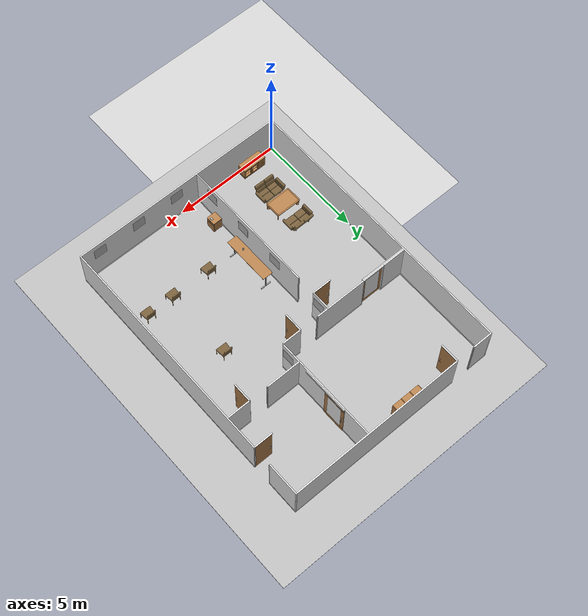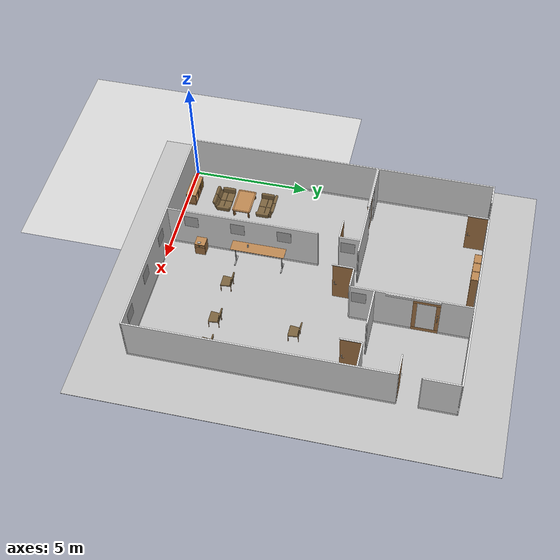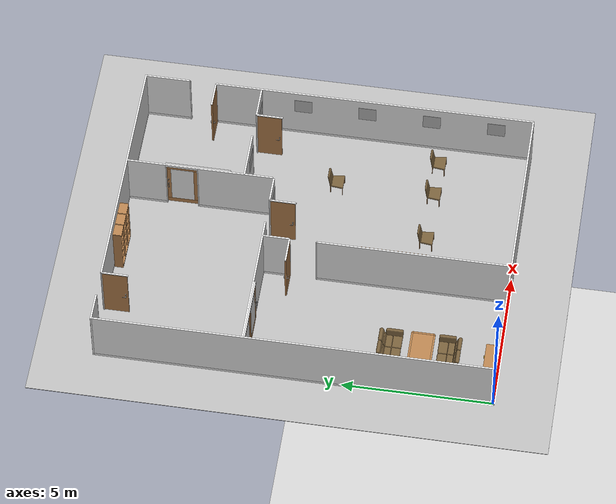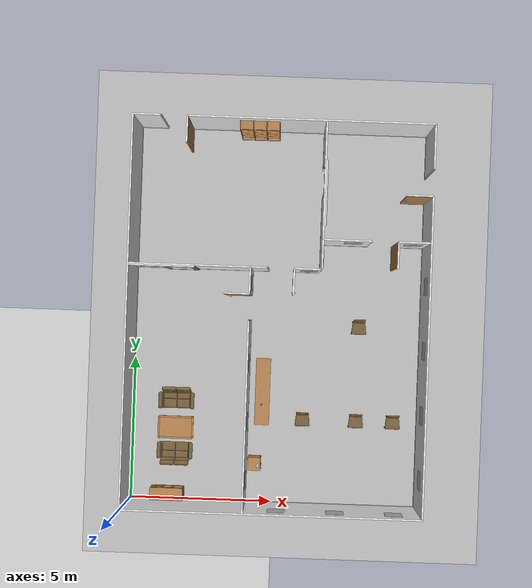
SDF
<sdf version="1.4">
 <world name="default">
  <scene>
   <ambient>0.5 0.5 0.5 1</ambient>
   <shadows>0</shadows>
   <grid>0</grid>
   <background>0.7 0.7 0.7 1</background>
  </scene>
  <physics type="ode">
   <real_time_update_rate>333.0</real_time_update_rate>
   <max_step_size>0.003</max_step_size>
   <ode><solver><type>quick</type><iters>100</iters></solver><constraints><cfm>0.0001</cfm></constraints></ode>
  </physics>
  <model name="gplane">
   <link name="body">
    <collision name="gplane_coll">
     <geometry><plane><normal>0 0 1</normal><size>10.075 13.18</size></plane></geometry>
     <surface><contact><ode><kp>1e+06</kp><kd>1</kd></ode></contact></surface>
     <laser_retro>2000</laser_retro>
    </collision>
    <visual name="gplane_vis">
     <geometry><plane><normal>0 0 1</normal><size>10.075 13.18</size></plane></geometry>
     <material>
      <script>
       <uri>model://base_materials/carpet/scripts</uri>
       <uri>model://base_materials/carpet/textures</uri>
       <name>carpet/carpet01</name>
      </script>
     </material>
     <cast_shadows>0</cast_shadows>
    </visual>
    <velocity_decay><linear>0</linear><angular>0</angular></velocity_decay>
   </link>
   <static>1</static>
  </model>
  <light name="inner_point_white1" type="point">
   <pose>4 5 4 0 0 0</pose>
   <diffuse>0.2 0.2 0.2 1</diffuse>
   <specular>0.1 0.1 0.1 1</specular>
   <attenuation>
    <range>20</range>
    <linear>0.1</linear>
    <constant>0.2</constant>
    <quadratic>0</quadratic>
   </attenuation>
   <cast_shadows>0</cast_shadows>
   <direction>0 0 -1</direction>
  </light>
  <light name="inner_point_white2" type="point">
   <pose>4 10 4 0 0 0</pose>
   <diffuse>0.2 0.2 0.2 1</diffuse>
   <specular>0.1 0.1 0.1 1</specular>
   <attenuation>
    <range>20</range>
    <linear>0.1</linear>
    <constant>0.2</constant>
    <quadratic>0</quadratic>
   </attenuation>
   <cast_shadows>0</cast_shadows>
   <direction>0 0 -1</direction>
  </light>
  <light name="inner_point_white3" type="point">
   <pose>8 5 4 0 0 0</pose>
   <diffuse>0.2 0.2 0.2 1</diffuse>
   <specular>0.1 0.1 0.1 1</specular>
   <attenuation>
    <range>20</range>
    <linear>0.1</linear>
    <constant>0.2</constant>
    <quadratic>0</quadratic>
   </attenuation>
   <cast_shadows>0</cast_shadows>
   <direction>0 0 -1</direction>
  </light>
  <light name="inner_point_white4" type="point">
   <pose>8 10 4 0 0 0</pose>
   <diffuse>0.2 0.2 0.2 1</diffuse>
   <specular>0.1 0.1 0.1 1</specular>
   <attenuation>
    <range>20</range>
    <linear>0.1</linear>
    <constant>0.2</constant>
    <quadratic>0</quadratic>
   </attenuation>
   <cast_shadows>0</cast_shadows>
   <direction>0 0 -1</direction>
  </light>
  <include><static>1</static><uri>model://full_inside_wall_april_tags</uri><name>inside_wall</name></include>
  <include><static>1</static><uri>model://full_outside_wall</uri><name>outside_wall</name></include>
  <include>
   <static>0</static>
   <pose>10.1025 10.8 0 0 0 1.5708</pose>
   <uri>model://openable_hinged_door_z_normally</uri>
   <name>door_x13y13</name>
  </include>
  <include>
   <static>1</static>
   <pose>10.1025 11.67 0 0 0 0</pose>
   <uri>model://hinged_door_stopper</uri>
   <name>door_stopper_x13y13</name>
  </include>
  <include>
   <static>0</static>
   <pose>1.8 13.2075 0 0 0 3.14</pose>
   <uri>model://openable_hinged_door_z_reversely</uri>
   <name>door_x02y16</name>
  </include>
  <include>
   <static>1</static>
   <pose>0.93 13.2075 0 0 0 1.5708</pose>
   <uri>model://hinged_door_stopper</uri>
   <name>door_stopper_x02y16</name>
  </include>
  <include>
   <static>0</static>
   <pose>4.075 7.33 0 0 0 1.5708</pose>
   <uri>model://openable_hinged_door_z_reversely</uri>
   <name>door_x05y09a</name>
  </include>
  <include>
   <static>1</static>
   <pose>4.075 6.425 0 0 0 0</pose>
   <uri>model://hinged_door_stopper</uri>
   <name>door_stopper_x05y09a</name>
  </include>
  <include>
   <static>0</static>
   <pose>1.65 8.23 0 0 0 -1.5708</pose>
   <uri>model://openable_sliding_door</uri>
   <name>door_x03y09</name>
  </include>
  <include>
   <static>0</static>
   <pose>5.5425 8.23 0 0 0 3.14</pose>
   <uri>model://openable_hinged_door_z_reversely</uri>
   <name>door_x08y09a</name>
  </include>
  <include>
   <static>1</static>
   <pose>4.675 8.23 0 0 0 1.5708</pose>
   <uri>model://hinged_door_stopper</uri>
   <name>door_stopper_x08y09a</name>
  </include>
  <include>
   <static>0</static>
   <pose>6.47 11.35 0 0 0 0</pose>
   <uri>model://openable_sliding_door</uri>
   <name>door_x08y13</name>
  </include>
  <include>
   <static>0</static>
   <pose>9.00 9.23 0 0 0 3.14</pose>
   <uri>model://openable_hinged_door_z_normally</uri>
   <name>door_x10y11</name>
  </include>
  <include>
   <static>1</static>
   <pose>8.13 9.23 0 0 0 1.5708</pose>
   <uri>model://hinged_door_stopper</uri>
   <name>door_stopper_x10y11</name>
  </include>
  <include><static>1</static><pose>4.6 1.2 0 0 0 0</pose><uri>model://wagon</uri><name>wagon</name></include>
  <include>
   <static>0</static>
   <pose>4.5 1.38 0.69 0 0 0</pose>
   <uri>model://nasal_inflammation_capsul</uri>
   <name>nasal_cupsul</name>
  </include>
  <include>
   <static>1</static>
   <pose>1.56 1.72 0 0 0 1.5708</pose>
   <uri>model://sofa-fix</uri>
   <name>sofa01</name>
  </include>
  <include>
   <static>1</static>
   <pose>1.56 3.56 0 0 0 -1.5708</pose>
   <uri>model://sofa-fix</uri>
   <name>sofa02</name>
  </include>
  <include>
   <static>1</static>
   <pose>1.56 2.58 0 0 0 1.5708</pose>
   <uri>model://kitchen_lowtable</uri>
   <name>kitchen_lowtable</name>
  </include>
  <include>
   <static>1</static>
   <pose>6.0184 3.0000 0.0000 0 0 -1.5708</pose>
   <uri>model://kitchen_chair</uri>
   <name>chair00</name>
  </include>
  <include>
   <static>1</static>
   <pose>7.9 3.0 0 0 0 -1.5708</pose>
   <uri>model://kitchen_chair</uri>
   <name>chair01</name>
  </include>
  <include>
   <static>1</static>
   <pose>9.2 3.0 0 0 0 -1.5708</pose>
   <uri>model://kitchen_chair</uri>
   <name>chair02</name>
  </include>
  <include>
   <static>1</static>
   <pose>7.9 6.3 0 0 0 -1.5708</pose>
   <uri>model://kitchen_chair</uri>
   <name>chair05</name>
  </include>
  <include>
   <static>0</static>
   <pose>1.9 0.47 0 0 0 1.5708</pose>
   <uri>model://openable_living_sideboard</uri>
   <name>living_sideboard</name>
  </include>
  <include>
   <static>0</static>
   <pose>0.997 0.274 0.505 0 0 0</pose>
   <uri>model://wallet</uri>
   <name>wallet</name>
  </include>
  <include>
   <static>1</static>
   <pose>4.6 4 0 0 0 0</pose>
   <uri>model://high_table</uri>
   <name>high_table01</name>
  </include>
  <include>
   <static>1</static>
   <pose>4.45 12.87 0 0 0 -1.5708</pose>
   <uri>model://high_shelf</uri>
   <name>high_shelf01</name>
  </include>
  <include>
   <static>1</static>
   <pose>4 12.87 0 0 0 -1.5708</pose>
   <uri>model://high_shelf</uri>
   <name>high_shelf02</name>
  </include>
  <include>
   <static>1</static>
   <pose>3.55 12.87 0 0 0 -1.5708</pose>
   <uri>model://high_shelf</uri>
   <name>high_shelf03</name>
  </include>
  <include>
   <static>0</static>
   <pose>4.5749 3.5577 1.1127 0 0 1</pose>
   <uri>model://hsr_orange</uri>
   <name>hsr_orange_02</name>
  </include>
  <include>
   <static>0</static>
   <pose>3.7459 12.9849 0.3794 0.0185 0.2284 -1.0179</pose>
   <uri>model://banana</uri>
   <name>banana_01</name>
  </include>
  <include>
   <static>0</static>
   <pose>3.8116 13.0323 1.2990 0.00 0.00 0.00</pose>
   <uri>model://pear</uri>
   <name>pear_01</name>
  </include>
  <include>
   <static>1</static>
   <pose>5.375 6.59 0 0 0 0</pose>
   <uri>model://lawn_garden</uri>
   <name>lawn_garden</name>
  </include>
 </world>
</sdf>

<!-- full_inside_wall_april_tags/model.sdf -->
<sdf version="1.4">
    <model name='full_inside_wall'>
      <link name='link'>
        <inertial>
          <mass>50</mass>
          <inertia>
            <ixx>1</ixx>
            <ixy>0</ixy>
            <ixz>0</ixz>
            <iyy>1</iyy>
            <iyz>0</iyz>
            <izz>1</izz>
          </inertia>
        </inertial>
        <visual name='x05y01_08_bottom_frame'>
          <pose>4.075 3.215 0.05 0 0 0</pose>
          <geometry>
            <box>
              <size>0.055 6.43 0.1</size>
            </box>
          </geometry>
          <material>
            <script>
              <uri>model://base_materials/color/scripts</uri>
              <name>hsr_color/white</name>
            </script>
          </material>
        </visual>
        <collision name='x05y01_08_collision_bottom_frame'>
          <pose>4.075 3.215 0.05 0 0 0</pose>
          <geometry>
            <box>
              <size>0.055 6.43 0.1</size>
            </box>
          </geometry>
          <max_contacts>10</max_contacts>
          <surface>
            <bounce/>
            <friction>
              <ode/>
            </friction>
            <contact>
              <ode/>
            </contact>
          </surface>
        </collision>
        <visual name='x05y01_08_wall'>
          <pose>4.075 3.215 1.095 0 0 0</pose>
          <geometry>
            <box>
              <size>0.055 6.43 1.99</size>
            </box>
          </geometry>
          <material>
            <script>
              <uri>model://base_materials/wall/scripts</uri>
              <uri>model://base_materials/wall/textures</uri>
              <name>wall/white_noise</name>
            </script>
          </material>
        </visual>
        <collision name='x05y01_08_collision_wall'>
          <pose>4.075 3.2150 1.095 0 0 0</pose>
          <geometry>
            <box>
              <size>0.055 6.43 1.99</size>
            </box>
          </geometry>
          <max_contacts>10</max_contacts>
          <surface>
            <bounce/>
            <friction>
              <ode/>
            </friction>
            <contact>
              <ode/>
            </contact>
          </surface>
        </collision>
        <visual name='x05y10_bottom_frame'>
          <pose>4.075 7.78 0.05 0 0 0</pose>
          <geometry>
            <box>
              <size>0.055 0.9 0.1</size>
            </box>
          </geometry>
          <material>
            <script>
              <uri>model://base_materials/color/scripts</uri>
              <name>hsr_color/white</name>
            </script>
          </material>
        </visual>
        <collision name='x05y10_collision_bottom_frame'>
          <pose>4.075 7.78 0.05 0 0 0</pose>
          <geometry>
            <box>
              <size>0.055 0.9 0.1</size>
            </box>
          </geometry>
          <max_contacts>10</max_contacts>
          <surface>
            <bounce/>
            <friction>
              <ode/>
            </friction>
            <contact>
              <ode/>
            </contact>
          </surface>
        </collision>
        <visual name='x05y10_wall'>
          <pose>4.075 7.78 1.095 0 0 0</pose>
          <geometry>
            <box>
              <size>0.055 0.9 1.99</size>
            </box>
          </geometry>
          <material>
            <script>
              <uri>model://base_materials/wall/scripts</uri>
              <uri>model://base_materials/wall/textures</uri>
              <name>wall/white_noise</name>
            </script>
          </material>
        </visual>
        <collision name='x05y10_collision_wall'>
          <pose>4.075 7.78 1.095 0 0 0</pose>
          <geometry>
            <box>
              <size>0.055 0.9 1.99</size>
            </box>
          </geometry>
          <max_contacts>10</max_contacts>
          <surface>
            <bounce/>
            <friction>
              <ode/>
            </friction>
            <contact>
              <ode/>
            </contact>
          </surface>
        </collision>

        <visual name='x01_02_y09_bottom_frame'>
          <pose>0.55 8.23 0.05 0 0 1.5708</pose>
          <geometry>
            <box>
              <size>0.055 1.1 0.1</size>
            </box>
          </geometry>
          <material>
            <script>
              <uri>model://base_materials/color/scripts</uri>
              <name>hsr_color/white</name>
            </script>
          </material>
        </visual>
        <collision name='x01_02_y09_collision_bottom_frame'>
          <pose>0.55 8.23 0.05 0 0 1.5708</pose>
          <geometry>
            <box>
              <size>0.055 1.1 0.1</size>
            </box>
          </geometry>
          <max_contacts>10</max_contacts>
          <surface>
            <bounce/>
            <friction>
              <ode/>
            </friction>
            <contact>
              <ode/>
            </contact>
          </surface>
        </collision>
        <visual name='x01_02_y09_wall'>
          <pose>0.55 8.23 1.095 0 0 1.5708</pose>
          <geometry>
            <box>
              <size>0.055 1.1 1.99</size>
            </box>
          </geometry>
          <material>
            <script>
              <uri>model://base_materials/wall/scripts</uri>
              <uri>model://base_materials/wall/textures</uri>
              <name>wall/white_noise</name>
            </script>
          </material>
        </visual>
        <collision name='x01_02_y09_collision_wall'>
          <pose>0.55 8.23 1.095 0 0 1.5708</pose>
          <geometry>
            <box>
              <size>0.055 1.1 1.99</size>
            </box>
          </geometry>
          <max_contacts>10</max_contacts>
          <surface>
            <bounce/>
            <friction>
              <ode/>
            </friction>
            <contact>
              <ode/>
            </contact>
          </surface>
        </collision>
        <visual name='x04_07_y09_bottom_frame'>
          <pose>3.42 8.23 0.05 0 0 1.5708</pose>
          <geometry>
            <box>
              <size>0.055 2.44 0.1</size>
            </box>
          </geometry>
          <material>
            <script>
              <uri>model://base_materials/color/scripts</uri>
              <name>hsr_color/white</name>
            </script>
          </material>
        </visual>
        <collision name='x04_07_y09_collision_bottom_frame'>
          <pose>3.42 8.23 0.05 0 0 1.5708</pose>
          <geometry>
            <box>
              <size>0.055 2.44 0.1</size>
            </box>
          </geometry>
          <max_contacts>10</max_contacts>
          <surface>
            <bounce/>
            <friction>
              <ode/>
            </friction>
            <contact>
              <ode/>
            </contact>
          </surface>
        </collision>
        <visual name='x04_07_y09_wall'>
          <pose>3.42 8.23 1.095 0 0 1.5708</pose>
          <geometry>
            <box>
              <size>0.055 2.44 1.99</size>
            </box>
          </geometry>
          <material>
            <script>
              <uri>model://base_materials/wall/scripts</uri>
              <uri>model://base_materials/wall/textures</uri>
              <name>wall/white_noise</name>
            </script>
          </material>
        </visual>
        <collision name='x04_07_y09_collision_wall'>
          <pose>3.42 8.23 1.095 0 0 1.5708</pose>
          <geometry>
            <box>
              <size>0.055 2.44 1.99</size>
            </box>
          </geometry>
          <max_contacts>10</max_contacts>
          <surface>
            <bounce/>
            <friction>
              <ode/>
            </friction>
            <contact>
              <ode/>
            </contact>
          </surface>
        </collision>
        <visual name='x08y10a_bottom_frame'>
          <pose>5.9925 8.23 0.05 0 0 1.5708</pose>
          <geometry>
            <box>
              <size>0.055 0.9 0.1</size>
            </box>
          </geometry>
          <material>
            <script>
              <uri>model://base_materials/color/scripts</uri>
              <name>hsr_color/white</name>
            </script>
          </material>
        </visual>
        <collision name='x08y10a_collision_bottom_frame'>
          <pose>5.9925 8.23 0.05 0 0 1.5708</pose>
          <geometry>
            <box>
              <size>0.055 0.9 0.1</size>
            </box>
          </geometry>
          <max_contacts>10</max_contacts>
          <surface>
            <bounce/>
            <friction>
              <ode/>
            </friction>
            <contact>
              <ode/>
            </contact>
          </surface>
        </collision>
        <visual name='x08y10a_wall'>
          <pose>5.9925 8.23 1.095 0 0 1.5708</pose>
          <geometry>
            <box>
              <size>0.055 0.9 1.99</size>
            </box>
          </geometry>
          <material>
            <script>
              <uri>model://base_materials/wall/scripts</uri>
              <uri>model://base_materials/wall/textures</uri>
              <name>wall/white_noise</name>
            </script>
          </material>
        </visual>
        <collision name='x08y10a_collision_wall'>
          <pose>5.9925 8.23 1.095 0 0 1.5708</pose>
          <geometry>
            <box>
              <size>0.055 0.9 1.99</size>
            </box>
          </geometry>
          <max_contacts>10</max_contacts>
          <surface>
            <bounce/>
            <friction>
              <ode/>
            </friction>
            <contact>
              <ode/>
            </contact>
          </surface>
        </collision>
        <visual name='x08y10a_bottom_frame'>
          <pose>5.9925 8.23 0.05 0 0 1.5708</pose>
          <geometry>
            <box>
              <size>0.055 0.9 0.1</size>
            </box>
          </geometry>
          <material>
            <script>
              <uri>model://base_materials/color/scripts</uri>
              <name>hsr_color/white</name>
            </script>
          </material>
        </visual>
        <collision name='x08y10a_collision_bottom_frame'>
          <pose>5.9925 8.23 0.05 0 0 1.5708</pose>
          <geometry>
            <box>
              <size>0.055 0.9 0.1</size>
            </box>
          </geometry>
          <max_contacts>10</max_contacts>
          <surface>
            <bounce/>
            <friction>
              <ode/>
            </friction>
            <contact>
              <ode/>
            </contact>
          </surface>
        </collision>
        <visual name='x08y10a_wall'>
          <pose>5.9925 8.23 1.095 0 0 1.5708</pose>
          <geometry>
            <box>
              <size>0.055 0.9 1.99</size>
            </box>
          </geometry>
          <material>
            <script>
              <uri>model://base_materials/wall/scripts</uri>
              <uri>model://base_materials/wall/textures</uri>
              <name>wall/white_noise</name>
            </script>
          </material>
        </visual>
        <collision name='x08y10a_collision_wall'>
          <pose>5.9925 8.23 1.095 0 0 1.5708</pose>
          <geometry>
            <box>
              <size>0.055 0.9 1.99</size>
            </box>
          </geometry>
          <max_contacts>10</max_contacts>
          <surface>
            <bounce/>
            <friction>
              <ode/>
            </friction>
            <contact>
              <ode/>
            </contact>
          </surface>
        </collision>
        <visual name='x08y14_15_bottom_frame'>
          <pose>6.47 12.54 0.05 0 0 0</pose>
          <geometry>
            <box>
              <size>0.055 1.28 0.1</size>
            </box>
          </geometry>
          <material>
            <script>
              <uri>model://base_materials/color/scripts</uri>
              <name>hsr_color/white</name>
            </script>
          </material>
        </visual>
        <collision name='x08y14_15_collision_bottom_frame'>
          <pose>6.47 12.54 0.05 0 0 0</pose>
          <geometry>
            <box>
              <size>0.055 1.28 0.1</size>
            </box>
          </geometry>
          <max_contacts>10</max_contacts>
          <surface>
            <bounce/>
            <friction>
              <ode/>
            </friction>
            <contact>
              <ode/>
            </contact>
          </surface>
        </collision>
        <visual name='x08y14_15_wall'>
          <pose>6.47 12.54 1.095 0 0 0</pose>
          <geometry>
            <box>
              <size>0.055 1.28 1.99</size>
            </box>
          </geometry>
          <material>
            <script>
              <uri>model://base_materials/wall/scripts</uri>
              <uri>model://base_materials/wall/textures</uri>
              <name>wall/white_noise</name>
            </script>
          </material>
        </visual>
        <collision name='x08y14_15_collision_wall'>
          <pose>6.47 12.54 1.095 0 0 0</pose>
          <geometry>
            <box>
              <size>0.055 1.28 1.99</size>
            </box>
          </geometry>
          <max_contacts>10</max_contacts>
          <surface>
            <bounce/>
            <friction>
              <ode/>
            </friction>
            <contact>
              <ode/>
            </contact>
          </surface>
        </collision>
        <visual name='x08y10b_12_bottom_frame'>
          <pose>6.47 9.52875 0.05 0 0 0</pose>
          <geometry>
            <box>
              <size>0.055 2.5425 0.1</size>
            </box>
          </geometry>
          <material>
            <script>
              <uri>model://base_materials/color/scripts</uri>
              <name>hsr_color/white</name>
            </script>
          </material>
        </visual>
        <collision name='x08y10b_12_collision_bottom_frame'>
          <pose>6.47 9.52875 0.05 0 0 0</pose>
          <geometry>
            <box>
              <size>0.055 2.5425 0.1</size>
            </box>
          </geometry>
          <max_contacts>10</max_contacts>
          <surface>
            <bounce/>
            <friction>
              <ode/>
            </friction>
            <contact>
              <ode/>
            </contact>
          </surface>
        </collision>
        <visual name='x08y10b_12_wall'>
          <pose>6.47 9.52875 1.095 0 0 0</pose>
          <geometry>
            <box>
              <size>0.055 2.5425 1.99</size>
            </box>
          </geometry>
          <material>
            <script>
              <uri>model://base_materials/wall/scripts</uri>
              <uri>model://base_materials/wall/textures</uri>
              <name>wall/white_noise</name>
            </script>
          </material>
        </visual>
        <collision name='x08y10b_12_collision_wall'>
          <pose>6.47 9.52875 1.095 0 0 0</pose>
          <geometry>
            <box>
              <size>0.055 2.5425 1.99</size>
            </box>
          </geometry>
          <max_contacts>10</max_contacts>
          <surface>
            <bounce/>
            <friction>
              <ode/>
            </friction>
            <contact>
              <ode/>
            </contact>
          </surface>
        </collision>
        <visual name='x08_09y11b_bottom_frame'>
          <pose>7.284 9.23 0.05 0 0 1.5708</pose>
          <geometry>
            <box>
              <size>0.055 1.632 0.1</size>
            </box>
          </geometry>
          <material>
            <script>
              <uri>model://base_materials/color/scripts</uri>
              <name>hsr_color/white</name>
            </script>
          </material>
        </visual>
        <collision name='x08_09y11b_collision_bottom_frame'>
          <pose>7.284 9.23 0.05 0 0 1.5708</pose>
          <geometry>
            <box>
              <size>0.055 1.632 0.1</size>
            </box>
          </geometry>
          <max_contacts>10</max_contacts>
          <surface>
            <bounce/>
            <friction>
              <ode/>
            </friction>
            <contact>
              <ode/>
            </contact>
          </surface>
        </collision>
        <visual name='x08_09y11b_wall'>
          <pose>7.284 9.23 1.095 0 0 1.5708</pose>
          <geometry>
            <box>
              <size>0.055 1.632 1.99</size>
            </box>
          </geometry>
          <material>
            <script>
              <uri>model://base_materials/wall/scripts</uri>
              <uri>model://base_materials/wall/textures</uri>
              <name>wall/white_noise</name>
            </script>
          </material>
        </visual>
        <collision name='x08_09y11b_collision_wall'>
          <pose>7.284 9.23 1.095 0 0 1.5708</pose>
          <geometry>
            <box>
              <size>0.055 1.632 1.99</size>
            </box>
          </geometry>
          <max_contacts>10</max_contacts>
          <surface>
            <bounce/>
            <friction>
              <ode/>
            </friction>
            <contact>
              <ode/>
            </contact>
          </surface>
        </collision>

        <visual name='x11_12y11_bottom_frame'>
          <pose>9.5375 9.23 0.05 0 0 1.5708</pose>
          <geometry>
            <box>
              <size>0.055 1.075 0.1</size>
            </box>
          </geometry>
          <material>
            <script>
              <uri>model://base_materials/color/scripts</uri>
              <name>hsr_color/white</name>
            </script>
          </material>
        </visual>
        <collision name='x11_12y11_collision_bottom_frame'>
          <pose>9.5375 9.23 0.05 0 0 1.5708</pose>
          <geometry>
            <box>
              <size>0.055 1.075 0.1</size>
            </box>
          </geometry>
          <max_contacts>10</max_contacts>
          <surface>
            <bounce/>
            <friction>
              <ode/>
            </friction>
            <contact>
              <ode/>
            </contact>
          </surface>
        </collision>
        <visual name='x11_12y11_wall'>
          <pose>9.5375 9.23 1.095 0 0 1.5708</pose>
          <geometry>
            <box>
              <size>0.055 1.075 1.99</size>
            </box>
          </geometry>
          <material>
            <script>
              <uri>model://base_materials/wall/scripts</uri>
              <uri>model://base_materials/wall/textures</uri>
              <name>wall/white_noise</name>
            </script>
          </material>
        </visual>
        <collision name='x11_12y11_collision_wall'>
          <pose>9.5375 9.23 1.095 0 0 1.5708</pose>
          <geometry>
            <box>
              <size>0.055 1.075 1.99</size>
            </box>
          </geometry>
          <max_contacts>10</max_contacts>
          <surface>
            <bounce/>
            <friction>
              <ode/>
            </friction>
            <contact>
              <ode/>
            </contact>
          </surface>
        </collision>

        <visual name='april_tag01'>
          <pose>4.11 1.0 1.5 0 0 0</pose>
          <geometry>
            <box>
              <size>0.01 0.6 0.6</size>
            </box>
          </geometry>
          <material>
            <script>
              <uri>model://april_tags/scripts</uri>
              <uri>model://april_tags/textures</uri>
              <name>april_tag/tag16h5_01</name>
            </script>
          </material>
        </visual>
        <visual name='april_tag02'>
          <pose>4.11 3.0 1.5 0 0 0</pose>
          <geometry>
            <box>
              <size>0.01 0.6 0.6</size>
            </box>
          </geometry>
          <material>
            <script>
              <uri>model://april_tags/scripts</uri>
              <uri>model://april_tags/textures</uri>
              <name>april_tag/tag16h5_02</name>
            </script>
          </material>
        </visual>
        <visual name='april_tag03'>
          <pose>4.11 5.0 1.5 0 0 0</pose>
          <geometry>
            <box>
              <size>0.01 0.6 0.6</size>
            </box>
          </geometry>
          <material>
            <script>
              <uri>model://april_tags/scripts</uri>
              <uri>model://april_tags/textures</uri>
              <name>april_tag/tag16h5_03</name>
            </script>
          </material>
        </visual>
        <visual name='april_tag04'>
          <pose>4.11 7.7 1.5 0 0 0</pose>
          <geometry>
            <box>
              <size>0.01 0.6 0.6</size>
            </box>
          </geometry>
          <material>
            <script>
              <uri>model://april_tags/scripts</uri>
              <uri>model://april_tags/textures</uri>
              <name>april_tag/tag16h5_04</name>
            </script>
          </material>
        </visual>
        <visual name='april_tag05'>
          <pose>6.05 8.18 1.5 0 0 0</pose>
          <geometry>
            <box>
              <size>0.6 0.01 0.6</size>
            </box>
          </geometry>
          <material>
            <script>
              <uri>model://april_tags/scripts</uri>
              <uri>model://april_tags/textures</uri>
              <name>april_tag/tag16h5_05</name>
            </script>
          </material>
        </visual>
        <visual name='april_tag06'>
          <pose>6.52 8.62 1.5 0 0 0</pose>
          <geometry>
            <box>
              <size>0.01 0.6 0.6</size>
            </box>
          </geometry>
          <material>
            <script>
              <uri>model://april_tags/scripts</uri>
              <uri>model://april_tags/textures</uri>
              <name>april_tag/tag16h5_06</name>
            </script>
          </material>
        </visual>
        <visual name='april_tag07'>
          <pose>7.51 9.18 1.5 0 0 0</pose>
          <geometry>
            <box>
              <size>0.6 0.01 0.6</size>
            </box>
          </geometry>
          <material>
            <script>
              <uri>model://april_tags/scripts</uri>
              <uri>model://april_tags/textures</uri>
              <name>april_tag/tag16h5_07</name>
            </script>
          </material>
        </visual>
        <visual name='april_tag08'>
          <pose>9.55 9.18 1.5 0 0 0</pose>
          <geometry>
            <box>
              <size>0.6 0.01 0.6</size>
            </box>
          </geometry>
          <material>
            <script>
              <uri>model://april_tags/scripts</uri>
              <uri>model://april_tags/textures</uri>
              <name>april_tag/tag16h5_08</name>
            </script>
          </material>
        </visual>
        <visual name='april_tag09'>
          <pose>10.03 1.2 1.5 0 0 0</pose>
          <geometry>
            <box>
              <size>0.01 0.6 0.6</size>
            </box>
          </geometry>
          <material>
            <script>
              <uri>model://april_tags/scripts</uri>
              <uri>model://april_tags/textures</uri>
              <name>april_tag/tag16h5_09</name>
            </script>
          </material>
        </visual>
        <visual name='april_tag10'>
          <pose>10.03 3.4 1.5 0 0 0</pose>
          <geometry>
            <box>
              <size>0.01 0.6 0.6</size>
            </box>
          </geometry>
          <material>
            <script>
              <uri>model://april_tags/scripts</uri>
              <uri>model://april_tags/textures</uri>
              <name>april_tag/tag16h5_10</name>
            </script>
          </material>
        </visual>
        <visual name='april_tag11'>
          <pose>10.03 5.6 1.5 0 0 0</pose>
          <geometry>
            <box>
              <size>0.01 0.6 0.6</size>
            </box>
          </geometry>
          <material>
            <script>
              <uri>model://april_tags/scripts</uri>
              <uri>model://april_tags/textures</uri>
              <name>april_tag/tag16h5_11</name>
            </script>
          </material>
        </visual>
        <visual name='april_tag12'>
          <pose>10.03 7.8 1.5 0 0 0</pose>
          <geometry>
            <box>
              <size>0.01 0.6 0.6</size>
            </box>
          </geometry>
          <material>
            <script>
              <uri>model://april_tags/scripts</uri>
              <uri>model://april_tags/textures</uri>
              <name>april_tag/tag16h5_12</name>
            </script>
          </material>
        </visual>
        <visual name='april_tag13'>
          <pose>5.2 0.0 1.5 0 0 0</pose>
          <geometry>
            <box>
              <size>0.6 0.01 0.6</size>
            </box>
          </geometry>
          <material>
            <script>
              <uri>model://april_tags/scripts</uri>
              <uri>model://april_tags/textures</uri>
              <name>april_tag/tag16h5_13</name>
            </script>
          </material>
        </visual>
        <visual name='april_tag14'>
          <pose>7.2 0.0 1.5 0 0 0</pose>
          <geometry>
            <box>
              <size>0.6 0.01 0.6</size>
            </box>
          </geometry>
          <material>
            <script>
              <uri>model://april_tags/scripts</uri>
              <uri>model://april_tags/textures</uri>
              <name>april_tag/tag16h5_14</name>
            </script>
          </material>
        </visual>
        <visual name='april_tag15'>
          <pose>9.2 0.0 1.5 0 0 0</pose>
          <geometry>
            <box>
              <size>0.6 0.01 0.6</size>
            </box>
          </geometry>
          <material>
            <script>
              <uri>model://april_tags/scripts</uri>
              <uri>model://april_tags/textures</uri>
              <name>april_tag/tag16h5_15</name>
            </script>
          </material>
        </visual>

        <velocity_decay>
          <linear>0</linear>
          <angular>0</angular>
        </velocity_decay>
        <self_collide>0</self_collide>
        <kinematic>0</kinematic>
        <gravity>1</gravity>
      </link>
      <static>1</static>
    </model>
</sdf>

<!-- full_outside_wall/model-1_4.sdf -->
<sdf version="1.4">
    <model name='full_outside_wall'>
      <link name='link'>
        <inertial>
          <mass>50</mass>
          <inertia>
            <ixx>1</ixx>
            <ixy>0</ixy>
            <ixz>0</ixz>
            <iyy>1</iyy>
            <iyz>0</iyz>
            <izz>1</izz>
          </inertia>
        </inertial>
        <visual name='x00_13y00_bottom_frame'>
          <pose>5.0375 -0.0275 0.05 0 0 0</pose>
          <geometry>
            <box>
              <size>10.185 0.055 0.1</size>
            </box>
          </geometry>
          <material>
            <script>
              <uri>model://base_materials/color/scripts</uri>
              <name>hsr_color/white</name>
            </script>
          </material>
        </visual>
        <collision name='x00_13y00_collision_bottom_frame'>
          <pose>5.0375 -0.0275 0.05 0 0 0</pose>
          <geometry>
            <box>
              <size>10.185 0.055 0.1</size>
            </box>
          </geometry>
          <max_contacts>10</max_contacts>
          <surface>
            <bounce/>
            <friction>
              <ode/>
            </friction>
            <contact>
              <ode/>
            </contact>
          </surface>
        </collision>
        <visual name='wall_x00_13y00'>
          <pose>5.0375 -0.0275 1.095 0 0 0</pose>
          <geometry>
            <box>
              <size>10.185 0.055 1.99</size>
            </box>
          </geometry>
          <material>
            <script>
              <uri>model://base_materials/wall/scripts</uri>
              <uri>model://base_materials/wall/textures</uri>
              <name>wall/white_noise</name>
            </script>
          </material>
        </visual>
        <collision name='wall_x00_13y00'>
          <pose>5.0375 -0.002 1.095 0 0 0</pose>
          <geometry>
            <box>
              <size>10.08 0.055 1.99</size>
            </box>
          </geometry>
          <max_contacts>10</max_contacts>
          <surface>
            <bounce/>
            <friction>
              <ode/>
            </friction>
            <contact>
              <ode/>
            </contact>
          </surface>
        </collision>
        <visual name='x00y00_15_bottom_frame'>
          <pose>-0.0275 6.59 0.05 0 0 0</pose>
          <geometry>
            <box>
              <size>0.055 13.29 0.1</size>
            </box>
          </geometry>
          <material>
            <script>
              <uri>model://base_materials/color/scripts</uri>
              <name>hsr_color/white</name>
            </script>
          </material>
        </visual>
        <collision name='x00y00_15_collision_bottom_frame'>
          <pose>-0.0275 6.59 0.05 0 0 0</pose>
          <geometry>
            <box>
              <size>0.055 13.29 0.1</size>
            </box>
          </geometry>
          <max_contacts>10</max_contacts>
          <surface>
            <bounce/>
            <friction>
              <ode/>
            </friction>
            <contact>
              <ode/>
            </contact>
          </surface>
        </collision>
        <visual name='wall_x00y00_15'>
          <pose>-0.0275 6.59 1.095 0 0 0</pose>
          <geometry>
            <box>
              <size>0.055 13.29 1.99</size>
            </box>
          </geometry>
          <material>
            <script>
              <uri>model://base_materials/wall/scripts</uri>
              <uri>model://base_materials/wall/textures</uri>
              <name>wall/white_noise</name>
            </script>
          </material>
        </visual>
        <collision name='wall_x00y00_x00y15'>
          <pose>-0.002 6.59 1.095 0 0 0</pose>
          <geometry>
            <box>
              <size>0.002 13.29 1.99</size>
            </box>
          </geometry>
          <max_contacts>10</max_contacts>
          <surface>
            <bounce/>
            <friction>
              <ode/>
            </friction>
            <contact>
              <ode/>
            </contact>
          </surface>
        </collision>
        <visual name='x13y00_12_bottom_frame'>
          <pose>10.1025 5.3725 0.05 0 0 0</pose>
          <geometry>
            <box>
              <size>0.055 10.855 0.1</size>
            </box>
          </geometry>
          <material>
            <script>
              <uri>model://base_materials/color/scripts</uri>
              <name>hsr_color/white</name>
            </script>
          </material>
        </visual>
        <collision name='x13y00_12_collision_bottom_frame'>
          <pose>10.1025 5.3725 0.05 0 0 0</pose>
          <geometry>
            <box>
              <size>0.055 10.855 0.1</size>
            </box>
          </geometry>
          <max_contacts>10</max_contacts>
          <surface>
            <bounce/>
            <friction>
              <ode/>
            </friction>
            <contact>
              <ode/>
            </contact>
          </surface>
        </collision>
        <visual name='wall_x13y00_12'>
          <pose>10.1025 5.3725 1.095 0 0 0</pose>
          <geometry>
            <box>
              <size>0.055 10.855 1.99</size>
            </box>
          </geometry>
          <material>
            <script>
              <uri>model://base_materials/wall/scripts</uri>
              <uri>model://base_materials/wall/textures</uri>
              <name>wall/white_noise</name>
            </script>
          </material>
        </visual>
        <collision name='wall_x13y00_12'>
          <pose>10.1025 5.3725 1.095 0 0 0</pose>
          <geometry>
            <box>
              <size>0.055 10.855 1.99</size>
            </box>
          </geometry>
          <max_contacts>10</max_contacts>
          <surface>
            <bounce/>
            <friction>
              <ode/>
            </friction>
            <contact>
              <ode/>
            </contact>
          </surface>
        </collision>
        <visual name='x13y14_16_bottom_frame'>
          <pose>10.1025 12.4675 0.05 0 0 0</pose>
          <geometry>
            <box>
              <size>0.055 1.535 0.1</size>
            </box>
          </geometry>
          <material>
            <script>
              <uri>model://base_materials/color/scripts</uri>
              <name>hsr_color/white</name>
            </script>
          </material>
        </visual>
        <collision name='x13y14_16_collision_bottom_frame'>
          <pose>10.1025 12.4675 0.05 0 0 0</pose>
          <geometry>
            <box>
              <size>0.055 1.535 0.1</size>
            </box>
          </geometry>
          <max_contacts>10</max_contacts>
          <surface>
            <bounce/>
            <friction>
              <ode/>
            </friction>
            <contact>
              <ode/>
            </contact>
          </surface>
        </collision>
        <visual name='wall_x13y14_x13y16'>
          <pose>10.1025 12.4675 1.095 0 0 0</pose>
          <geometry>
            <box>
              <size>0.055 1.535 1.99</size>
            </box>
          </geometry>
          <material>
            <script>
              <uri>model://base_materials/wall/scripts</uri>
              <uri>model://base_materials/wall/textures</uri>
              <name>wall/white_noise</name>
            </script>
          </material>
        </visual>
        <collision name='wall_x13y14_x13y16'>
          <pose>10.1025 12.4675 1.095 0 0 0</pose>
          <geometry>
            <box>
              <size>0.055 1.535 1.99</size>
            </box>
          </geometry>
          <max_contacts>10</max_contacts>
          <surface>
            <bounce/>
            <friction>
              <ode/>
            </friction>
            <contact>
              <ode/>
            </contact>
          </surface>
        </collision>
        <visual name='x00_01y16_bottom_frame'>
          <pose>0.4225 13.2075 0.05 0 0 0</pose>
          <geometry>
            <box>
              <size>0.955 0.055 0.1</size>
            </box>
          </geometry>
          <material>
            <script>
              <uri>model://base_materials/color/scripts</uri>
              <name>hsr_color/white</name>
            </script>
          </material>
        </visual>
        <collision name='x00_01y16_collision_bottom_frame'>
          <pose>0.4225 13.2075 0.05 0 0 0</pose>
          <geometry>
            <box>
              <size>0.955 0.055 0.1</size>
            </box>
          </geometry>
          <max_contacts>10</max_contacts>
          <surface>
            <bounce/>
            <friction>
              <ode/>
            </friction>
            <contact>
              <ode/>
            </contact>
          </surface>
        </collision>
        <visual name='wall_x00_01y16'>
          <pose>0.4225 13.2075 1.095 0 0 0</pose>
          <geometry>
            <box>
              <size>0.955 0.055 1.99</size>
            </box>
          </geometry>
          <material>
            <script>
              <uri>model://base_materials/wall/scripts</uri>
              <uri>model://base_materials/wall/textures</uri>
              <name>wall/white_noise</name>
            </script>
          </material>
        </visual>
        <collision name='wall_x00_x01y16'>
          <pose>0.4225 13.2075 1.095 0 0 0</pose>
          <geometry>
            <box>
              <size>0.955 0.055 1.99</size>
            </box>
          </geometry>
          <max_contacts>10</max_contacts>
          <surface>
            <bounce/>
            <friction>
              <ode/>
            </friction>
            <contact>
              <ode/>
            </contact>
          </surface>
        </collision>

        <visual name='x03_13y16_bottom_frame'>
          <pose>5.965 13.2075 0.05 0 0 0</pose>
          <geometry>
            <box>
              <size>8.330 0.05 0.1</size>
            </box>
          </geometry>
          <material>
            <script>
              <uri>model://base_materials/color/scripts</uri>
              <name>hsr_color/white</name>
            </script>
          </material>
        </visual>
        <collision name='x03_13y16_collision_bottom_frame'>
          <pose>5.965 13.2075 0.05 0 0 0</pose>
          <geometry>
            <box>
              <size>8.330 0.05 0.1</size>
            </box>
          </geometry>
          <max_contacts>10</max_contacts>
          <surface>
            <bounce/>
            <friction>
              <ode/>
            </friction>
            <contact>
              <ode/>
            </contact>
          </surface>
        </collision>
        <visual name='wall_x03_13y16'>
          <pose>5.965 13.2075 1.095 0 0 0</pose>
          <geometry>
            <box>
              <size>8.330 0.055 1.99</size>
            </box>
          </geometry>
          <material>
            <script>
              <uri>model://base_materials/wall/scripts</uri>
              <uri>model://base_materials/wall/textures</uri>
              <name>wall/white_noise</name>
            </script>
          </material>
        </visual>
        <collision name='wall_x03_13y16'>
          <pose>5.965 13.2075 1.095 0 0 0</pose>
          <geometry>
            <box>
              <size>8.330 0.055 1.99</size>
            </box>
          </geometry>
          <max_contacts>10</max_contacts>
          <surface>
            <bounce/>
            <friction>
              <ode/>
            </friction>
            <contact>
              <ode/>
            </contact>
          </surface>
        </collision>

        <velocity_decay>
          <linear>0</linear>
          <angular>0</angular>
        </velocity_decay>
        <self_collide>0</self_collide>
        <kinematic>0</kinematic>
        <gravity>1</gravity>
      </link>
      <static>1</static>
    </model>
</sdf>

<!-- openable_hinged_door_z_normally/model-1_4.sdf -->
<sdf version="1.4">
    <model name='openable_hinged_door_z_normally'>
      <joint name="frame_to_world_joint" type="revolute">
          <parent>world</parent>
          <child>frame</child>
          <!-- Mimic fixed joint  -->
          <pose>0 -0.45 0 0 0 0</pose>
          <axis>
              <xyz>0 0 1</xyz>
              <limit>
                  <lower>0</lower>
                  <upper>0</upper>
              </limit>
          </axis>
      </joint>
      <link name='frame'>
        <pose>0 0.45 0 0 0 0</pose>
        <visual name='left_frame'>
          <pose>0 -0.4325 1.025 0 0 0</pose>
          <geometry>
            <box>
              <size>0.055 0.035 2.050</size>
            </box>
          </geometry>
          <material>
            <script>
              <uri>model://base_materials/color/scripts</uri>
              <name>hsr_color/white</name>
            </script>
          </material>
        </visual>
        <collision name='collision_left_frame'>
          <pose>0 -0.4325 1.025 0 0 0</pose>
          <geometry>
            <box>
              <size>0.055 0.035 2.050</size>
            </box>
          </geometry>
          <max_contacts>10</max_contacts>
          <surface>
            <bounce/>
            <friction>
              <ode/>
            </friction>
            <contact>
              <ode/>
            </contact>
          </surface>
        </collision>
        <visual name='top_frame'>
          <pose>0 0 2.070 0 0 0</pose>
          <geometry>
            <box>
              <size>0.055 0.9 0.04</size>
            </box>
          </geometry>
          <material>
            <script>
              <uri>model://base_materials/color/scripts</uri>
              <name>hsr_color/white</name>
            </script>
          </material>
        </visual>
        <collision name='collision_top_frame'>
          <pose>0 0 2.070 0 0 0</pose>
          <geometry>
            <box>
              <size>0.055 0.9 0.04</size>
            </box>
          </geometry>
          <max_contacts>10</max_contacts>
          <surface>
            <bounce/>
            <friction>
              <ode/>
            </friction>
            <contact>
              <ode/>
            </contact>
          </surface>
        </collision>
        <velocity_decay>
          <linear>0</linear>
          <angular>0</angular>
        </velocity_decay>
        <self_collide>0</self_collide>
        <kinematic>0</kinematic>
        <gravity>1</gravity>
      </link>
      <link name='door'>
        <pose>0 0 0 0 0 0</pose>
        <inertial>
          <mass>50</mass>
          <inertia>
            <ixx>14.2</ixx>
            <ixy>0</ixy>
            <ixz>0</ixz>
            <iyy>17.2</iyy>
            <iyz>0</iyz>
            <izz>3.0</izz>
          </inertia>
        </inertial>
        <visual name='door'>
          <pose>0 0.45 1.050 0 0 0</pose>
          <geometry>
            <box>
              <size>0.055 0.830 2.0</size>
            </box>
          </geometry>
          <material>
            <script>
              <uri>model://base_materials/wood/scripts/wood.material</uri>
              <name>base_materials/wood</name>
            </script>
          </material>
        </visual>
        <collision name='collision_door'>
          <pose>0 0.45 1.050 0 0 0</pose>
          <geometry>
            <box>
              <size>0.055 0.830 2.0</size>
            </box>
          </geometry>
          <max_contacts>10</max_contacts>
          <surface>
            <bounce/>
            <friction>
              <ode/>
            </friction>
            <contact>
              <ode/>
            </contact>
          </surface>
        </collision>
        <visual name='handle_lock1'>
          <pose>0 0.785 1.03 0 0 0</pose>
          <geometry>
            <box>
              <size>0.075 0.005 0.04</size>
            </box>
          </geometry>
          <material>
            <script>
              <uri>model://base_materials/color/scripts</uri>
              <name>hsr_color/white</name>
            </script>
          </material>
        </visual>
        <visual name='handle_lock2'>
          <pose>0 0.785 1.03 0 1.5708 0</pose>
          <geometry>
            <cylinder>
              <radius>0.025</radius>
              <length>0.065</length>
            </cylinder>
          </geometry>
          <material>
            <script>
              <uri>model://base_materials/color/scripts</uri>
              <name>hsr_color/white</name>
            </script>
          </material>
        </visual>
        <velocity_decay>
          <linear>0</linear>
          <angular>0</angular>
        </velocity_decay>
        <self_collide>0</self_collide>
        <kinematic>0</kinematic>
        <gravity>1</gravity>
      </link>
      <link name='handles'>
        <pose>0.0 0.8 0.93 0 3.14 1.57</pose>
        <visual name="handle1_visual">
          <pose>0.015 0 0 -1.57 0 0</pose>
          <geometry>
            <mesh>
              <uri>model://openable_hinged_door_z_normally/meshes/door_handle_small.dae</uri>
            </mesh>
          </geometry>
        </visual>
        <collision name="handle1_collision">
          <pose>0.015 0 0 -1.57 0 0</pose>
          <geometry>
            <mesh>
              <uri>model://openable_hinged_door_z_normally/meshes/door_handle_small.dae</uri>
            </mesh>
          </geometry>
        </collision>
      </link>
      <joint name="handle" type="revolute">
        <parent>door</parent>
        <child>handles</child>
        <pose>0.013 0 0 0 0 0</pose>
        <axis>
          <xyz>1 0 0</xyz>
          <limit>
            <lower>0</lower>
            <upper>0.52</upper>
          </limit>
          <dynamics>
            <damping>0.1</damping>
            <spring_stiffness>0.3</spring_stiffness>
          </dynamics>
        </axis>
        <physics>
          <ode>
            <cfm_damping>1</cfm_damping>
          </ode>
        </physics>
      </joint>
      <joint name="hinge" type="revolute">
        <parent>frame</parent>
        <child>door</child>
        <axis>
          <xyz>0 0 1</xyz>
          <limit>
            <lower>0</lower>
            <upper>1.58</upper>
            <effort></effort>
            <velocity></velocity>
          </limit>
          <dynamics>
            <damping>1.0</damping>
            <friction>1.0</friction>
          </dynamics>
        </axis>
        <physics>
          <ode>
            <cfm_damping>1</cfm_damping>
          </ode>
        </physics>
      </joint>
      <static>0</static>
    </model>
</sdf>

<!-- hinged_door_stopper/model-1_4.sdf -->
<sdf version="1.4">
<model name='hinged_door_stopper'>
  <link name='door_frame'>
    <pose>0 0 0 0 0 0</pose>
    <visual name='stopper'>
      <pose>0.0225 0.0175 1.025 0 0 0</pose>
      <geometry>
        <box>
          <size>0.01 0.035 2.050</size>
        </box>
      </geometry>
      <material>
        <script>
          <uri>model://base_materials/color/scripts</uri>
          <name>hsr_color/white</name>
        </script>
      </material>
    </visual>
    <collision name='collision_frame_1'>
      <pose>0.0225 0.0175 1.025 0 0 0</pose>
      <geometry>
        <box>
          <size>0.01 0.035 2.050</size>
        </box>
      </geometry>
      <max_contacts>10</max_contacts>
      <surface/>
    </collision>
    <visual name='frame_2'>
      <pose>-0.0225 0.0175 1.025 0 0 0</pose>
      <geometry>
        <box>
          <size>0.01 0.035 2.050</size>
        </box>
      </geometry>
      <material>
        <script>
          <uri>model://base_materials/color/scripts</uri>
          <name>hsr_color/white</name>
        </script>
      </material>
    </visual>
    <collision name='collision_frame_2'>
      <pose>-0.0225 0.0175 1.025 0 0 0</pose>
      <geometry>
        <box>
          <size>0.01 0.035 2.050</size>
        </box>
      </geometry>
      <max_contacts>10</max_contacts>
      <surface/>
    </collision>
  </link>
  <static>0</static>
</model>
</sdf>

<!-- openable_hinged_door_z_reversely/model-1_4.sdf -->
<sdf version="1.4">
    <model name='openable_hinged_door_z_reversely'>
      <joint name="frame_to_world_joint" type="revolute">
          <parent>world</parent>
          <child>frame</child>
          <!-- Mimic fixed joint  -->
          <pose>0 -0.45 0 0 0 0</pose>
          <axis>
              <xyz>0 0 1</xyz>
              <limit>
                  <lower>0</lower>
                  <upper>0</upper>
              </limit>
          </axis>
      </joint>
      <link name='frame'>
        <pose>0 0.45 0 0 0 0</pose>
        <visual name='left_frame'>
          <pose>0 -0.4325 1.025 0 0 0</pose>
          <geometry>
            <box>
              <size>0.055 0.035 2.050</size>
            </box>
          </geometry>
          <material>
            <script>
              <uri>model://base_materials/color/scripts</uri>
              <name>hsr_color/white</name>
            </script>
          </material>
        </visual>
        <collision name='collision_left_frame'>
          <pose>0 -0.4325 1.025 0 0 0</pose>
          <geometry>
            <box>
              <size>0.055 0.035 2.050</size>
            </box>
          </geometry>
          <max_contacts>10</max_contacts>
          <surface>
            <bounce/>
            <friction>
              <ode/>
            </friction>
            <contact>
              <ode/>
            </contact>
          </surface>
        </collision>
        <visual name='top_frame'>
          <pose>0 0 2.070 0 0 0</pose>
          <geometry>
            <box>
              <size>0.055 0.9 0.04</size>
            </box>
          </geometry>
          <material>
            <script>
              <uri>model://base_materials/color/scripts</uri>
              <name>hsr_color/white</name>
            </script>
          </material>
        </visual>
        <collision name='collision_top_frame'>
          <pose>0 0 2.070 0 0 0</pose>
          <geometry>
            <box>
              <size>0.055 0.9 0.04</size>
            </box>
          </geometry>
          <max_contacts>10</max_contacts>
          <surface>
            <bounce/>
            <friction>
              <ode/>
            </friction>
            <contact>
              <ode/>
            </contact>
          </surface>
        </collision>
        <velocity_decay>
          <linear>0</linear>
          <angular>0</angular>
        </velocity_decay>
        <self_collide>0</self_collide>
        <kinematic>0</kinematic>
        <gravity>1</gravity>
      </link>
      <link name='door'>
        <pose>0 0 0 0 0 0</pose>
        <inertial>
          <mass>50</mass>
          <inertia>
            <ixx>14.2</ixx>
            <ixy>0</ixy>
            <ixz>0</ixz>
            <iyy>17.2</iyy>
            <iyz>0</iyz>
            <izz>3.0</izz>
          </inertia>
        </inertial>
        <visual name='door'>
          <pose>0 0.45 1.050 0 0 0</pose>
          <geometry>
            <box>
              <size>0.055 0.830 2.0</size>
            </box>
          </geometry>
          <material>
            <script>
              <uri>model://base_materials/wood/scripts/wood.material</uri>
              <name>base_materials/wood</name>
            </script>
          </material>
        </visual>
        <collision name='collision_door'>
          <pose>0 0.45 1.050 0 0 0</pose>
          <geometry>
            <box>
              <size>0.055 0.830 2.0</size>
            </box>
          </geometry>
          <max_contacts>10</max_contacts>
          <surface>
            <bounce/>
            <friction>
              <ode/>
            </friction>
            <contact>
              <ode/>
            </contact>
          </surface>
        </collision>
        <visual name='handle_lock1'>
          <pose>0 0.785 1.03 0 0 0</pose>
          <geometry>
            <box>
              <size>0.075 0.005 0.04</size>
            </box>
          </geometry>
          <material>
            <script>
              <uri>model://base_materials/color/scripts</uri>
              <name>hsr_color/white</name>
            </script>
          </material>
        </visual>
        <visual name='handle_lock2'>
          <pose>0 0.785 1.03 0 1.5708 0</pose>
          <geometry>
            <cylinder>
              <radius>0.025</radius>
              <length>0.065</length>
            </cylinder>
          </geometry>
          <material>
            <script>
              <uri>model://base_materials/color/scripts</uri>
              <name>hsr_color/white</name>
            </script>
          </material>
        </visual>
        <velocity_decay>
          <linear>0</linear>
          <angular>0</angular>
        </velocity_decay>
        <self_collide>0</self_collide>
        <kinematic>0</kinematic>
        <gravity>1</gravity>
      </link>
      <link name='handles'>
        <pose>0.0 0.8 0.93 0 3.14 1.57</pose>
        <visual name="handle1_visual">
          <pose>0.015 0 0 -1.57 0 0</pose>
          <geometry>
            <mesh>
              <uri>model://openable_hinged_door_z_normally/meshes/door_handle_small.dae</uri>
            </mesh>
          </geometry>
        </visual>
        <collision name="handle1_collision">
          <pose>0.015 0 0 -1.57 0 0</pose>
          <geometry>
            <mesh>
              <uri>model://openable_hinged_door_z_normally/meshes/door_handle_small.dae</uri>
            </mesh>
          </geometry>
        </collision>
      </link>
      <joint name="handle" type="revolute">
        <parent>door</parent>
        <child>handles</child>
        <pose>0.013 0 0 0 0 0</pose>
        <axis>
          <xyz>1 0 0</xyz>
          <limit>
            <lower>0</lower>
            <upper>0.52</upper>
          </limit>
          <dynamics>
            <damping>0.1</damping>
            <spring_stiffness>0.3</spring_stiffness>
          </dynamics>
        </axis>
        <physics>
          <ode>
            <cfm_damping>1</cfm_damping>
          </ode>
        </physics>
      </joint>
      <joint name="hinge" type="revolute">
        <parent>frame</parent>
        <child>door</child>
        <axis>
          <xyz>0 0 1</xyz>
          <limit>
            <lower>-1.58</lower>
            <upper>0</upper>
            <effort></effort>
            <velocity></velocity>
          </limit>
          <dynamics>
            <damping>1.0</damping>
            <friction>1.0</friction>
          </dynamics>
        </axis>
        <physics>
          <ode>
            <cfm_damping>1</cfm_damping>
          </ode>
        </physics>
      </joint>
      <static>0</static>
    </model>
</sdf>

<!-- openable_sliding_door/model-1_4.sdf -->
<sdf version="1.4">
    <model name='openable_sliding_door'>
      <joint name="frame_to_world_joint" type="revolute">
          <parent>world</parent>
          <child>frame</child>
          <!-- Mimic fixed joint  -->
          <axis>
              <xyz>0 0 1</xyz>
              <limit>
                  <upper>0</upper>
                  <lower>0</lower>
              </limit>
          </axis>
      </joint>
      <link name='frame'>
        <inertial>
          <mass>50</mass>
          <inertia>
            <ixx>1</ixx>
            <ixy>0</ixy>
            <ixz>0</ixz>
            <iyy>1</iyy>
            <iyz>0</iyz>
            <izz>1</izz>
          </inertia>
        </inertial>
        <visual name='right_frame'>
          <pose>0 0.5325 0.995 0 0 0</pose>
          <geometry>
            <box>
              <size>0.055 0.035 1.990</size>
            </box>
          </geometry>
          <material>
            <script>
              <uri>model://base_materials/color/scripts</uri>
              <name>hsr_color/white</name>
            </script>
          </material>
        </visual>
        <collision name='collision_right_frame'>
          <pose>0 0.5325 0.995 0 0 0</pose>
          <geometry>
            <box>
              <size>0.055 0.035 1.990</size>
            </box>
          </geometry>
          <max_contacts>10</max_contacts>
          <surface>
            <bounce/>
            <friction>
              <ode/>
            </friction>
            <contact>
              <ode/>
            </contact>
          </surface>
        </collision>
        <visual name='left_frame'>
          <pose>0 -0.5325 0.995 0 0 0</pose>
          <geometry>
            <box>
              <size>0.055 0.035 1.990</size>
            </box>
          </geometry>
          <material>
            <script>
              <uri>model://base_materials/color/scripts</uri>
              <name>hsr_color/white</name>
            </script>
          </material>
        </visual>
        <collision name='collision_left_frame'>
          <pose>0 -0.5325 0.995 0 0 0</pose>
          <geometry>
            <box>
              <size>0.055 0.035 1.990</size>
            </box>
          </geometry>
          <max_contacts>10</max_contacts>
          <surface>
            <bounce/>
            <friction>
              <ode/>
            </friction>
            <contact>
              <ode/>
            </contact>
          </surface>
        </collision>
        <visual name='top_frame'>
          <pose>0 0 2.040 0 0 0</pose>
          <geometry>
            <box>
              <size>0.055 1.1 0.1</size>
            </box>
          </geometry>
          <material>
            <script>
              <uri>model://base_materials/color/scripts</uri>
              <name>hsr_color/white</name>
            </script>
          </material>
        </visual>
        <collision name='collision_top_frame'>
          <pose>0 0 2.040 0 0 0</pose>
          <geometry>
            <box>
              <size>0.055 1.1 0.1</size>
            </box>
          </geometry>
          <max_contacts>10</max_contacts>
          <surface>
            <bounce/>
            <friction>
              <ode/>
            </friction>
            <contact>
              <ode/>
            </contact>
          </surface>
        </collision>

        <visual name='top_guard'>
          <pose>0.05 -0.55 2.065 0 0 0</pose>
          <geometry>
            <box>
              <size>0.045 2.2 0.05</size>
            </box>
          </geometry>
          <material>
            <script>
              <uri>model://base_materials/color/scripts</uri>
              <name>hsr_color/white</name>
            </script>
          </material>
        </visual>
        <collision name='collision_top_guard'>
          <pose>0.05 -0.55 2.065 0 0 0</pose>
          <geometry>
            <box>
              <size>0.045 2.2 0.05</size>
            </box>
          </geometry>
          <max_contacts>10</max_contacts>
          <surface>
            <bounce/>
            <friction>
              <ode/>
            </friction>
            <contact>
              <ode/>
            </contact>
          </surface>
        </collision>
        <visual name='front_guard'>
          <pose>0.0825 -0.55 2.04 0 0 0</pose>
          <geometry>
            <box>
              <size>0.020 2.2 0.10</size>
            </box>
          </geometry>
          <material>
            <script>
              <uri>model://base_materials/color/scripts</uri>
              <name>hsr_color/white</name>
            </script>
          </material>
        </visual>
        <collision name='collision_front_guard'>
          <pose>0.0825 -0.55 2.04 0 0 0</pose>
          <geometry>
            <box>
              <size>0.020 2.2 0.10</size>
            </box>
          </geometry>
          <max_contacts>10</max_contacts>
          <surface>
            <bounce/>
            <friction>
              <ode/>
            </friction>
            <contact>
              <ode/>
            </contact>
          </surface>
        </collision>
      </link>
      <link name='door'>
        <pose>-0.0275 0 0 0 0 0</pose>
        <visual name='glass'>
          <pose>0.0775 0 1.0250 0 0 0</pose>
          <geometry>
            <box>
              <size>0.030 0.77 1.580</size>
            </box>
          </geometry>
          <material>
            <script>
              <name>hsr_color/white_transparency1</name>
              <name>hsr_color/cornflowerblue_transparency1</name>
            </script>
          </material>
        </visual>
        <collision name='collision_glass'>
          <pose>0.0775 0 1.0250 0 0 0</pose>
          <geometry>
            <box>
              <size>0.030 0.77 1.580</size>
            </box>
          </geometry>
          <max_contacts>10</max_contacts>
          <surface>
            <bounce/>
            <friction>
              <ode/>
            </friction>
            <contact>
              <ode/>
            </contact>
          </surface>
        </collision>
        <visual name='top_frame'>
          <pose>0.0775 0 1.9075 0 0 0</pose>
          <geometry>
            <box>
              <size>0.030 1.1 0.185</size>
            </box>
          </geometry>
          <material>
            <script>
              <uri>model://base_materials/wood/scripts/wood.material</uri>
              <name>base_materials/wood</name>
            </script>
          </material>
        </visual>
        <collision name='collision_top_frame'>
          <pose>0.0775 0 1.9075 0 0 0</pose>
          <geometry>
            <box>
              <size>0.030 1.1 0.185</size>
            </box>
          </geometry>
          <max_contacts>10</max_contacts>
          <surface>
            <bounce/>
            <friction>
              <ode/>
            </friction>
            <contact>
              <ode/>
            </contact>
          </surface>
        </collision>
        <visual name='right_frame'>
          <pose>0.0775 0.4675 1.0250 0 0 0</pose>
          <geometry>
            <box>
              <size>0.030 0.165 1.580</size>
            </box>
          </geometry>
          <material>
            <script>
              <uri>model://base_materials/wood/scripts/wood.material</uri>
              <name>base_materials/wood</name>
            </script>
          </material>
        </visual>
        <collision name='collision_right_frame'>
          <pose>0.0775 0.4675 1.0250 0 0 0</pose>
          <geometry>
            <box>
              <size>0.030 0.165 1.580</size>
            </box>
          </geometry>
          <max_contacts>10</max_contacts>
          <surface>
            <bounce/>
            <friction>
              <ode/>
            </friction>
            <contact>
              <ode/>
            </contact>
          </surface>
        </collision>
        <visual name='left_frame'>
          <pose>0.0775 -0.4675 1.0250 0 0 0</pose>
          <geometry>
            <box>
              <size>0.030 0.165 1.580</size>
            </box>
          </geometry>
          <material>
            <script>
              <uri>model://base_materials/wood/scripts/wood.material</uri>
              <name>base_materials/wood</name>
            </script>
          </material>
        </visual>
        <collision name='collision_left_frame'>
          <pose>0.0775 -0.4675 1.0250 0 0 0</pose>
          <geometry>
            <box>
              <size>0.030 0.165 1.580</size>
            </box>
          </geometry>
          <max_contacts>10</max_contacts>
          <surface>
            <bounce/>
            <friction>
              <ode/>
            </friction>
            <contact>
              <ode/>
            </contact>
          </surface>
        </collision>
        <visual name='bottom_frame'>
          <pose>0.0775 0 0.1425 0 0 0</pose>
          <geometry>
            <box>
              <size>0.030 1.1 0.185</size>
            </box>
          </geometry>
          <material>
            <script>
              <uri>model://base_materials/wood/scripts/wood.material</uri>
              <name>base_materials/wood</name>
            </script>
          </material>
        </visual>
        <collision name='collision_bottom_frame'>
          <pose>0.0775 0 0.1425 0 0 0</pose>
          <geometry>
            <box>
              <size>0.030 1.1 0.185</size>
            </box>
          </geometry>
          <max_contacts>10</max_contacts>
          <surface>
            <bounce/>
            <friction>
              <ode/>
            </friction>
            <contact>
              <ode/>
            </contact>
          </surface>
        </collision>
        <visual name='handle_top_frame'>
          <pose>0.0775 0.4675 1.0675 0 1.5708 0</pose>
          <geometry>
            <cylinder>
              <radius>0.0125</radius>
              <length>0.125</length>
            </cylinder>
          </geometry>
          <material>
            <script>
              <uri>model://base_materials/color/scripts</uri>
              <name>hsr_color/grey</name>
            </script>
          </material>
        </visual>
        <collision name='collision_handle_top_frame'>
          <pose>0.0775 0.4675 1.0675 0 1.5708 0</pose>
          <geometry>
            <cylinder>
              <radius>0.0125</radius>
              <length>0.125</length>
            </cylinder>
          </geometry>
          <max_contacts>10</max_contacts>
          <surface>
            <bounce/>
            <friction>
              <ode/>
            </friction>
            <contact>
              <ode/>
            </contact>
          </surface>
        </collision>
        <visual name='handle_bottom_frame'>
          <pose>0.0775 0.4675 0.8425 0 1.5708 0</pose>
          <geometry>
            <cylinder>
              <radius>0.0125</radius>
              <length>0.125</length>
            </cylinder>
          </geometry>
          <material>
            <script>
              <uri>model://base_materials/color/scripts</uri>
              <name>hsr_color/grey</name>
            </script>
          </material>
        </visual>
        <collision name='collision_handle_bottom_frame'>
          <pose>0.0775 0.4675 0.8425 0 1.5708 0</pose>
          <geometry>
            <cylinder>
              <radius>0.0125</radius>
              <length>0.125</length>
            </cylinder>
          </geometry>
          <max_contacts>10</max_contacts>
          <surface>
            <bounce/>
            <friction>
              <ode/>
            </friction>
            <contact>
              <ode/>
            </contact>
          </surface>
        </collision>
        <visual name='handle_front_frame'>
          <pose>0.14 0.4675 0.955 0 0 0</pose>
          <geometry>
            <cylinder>
              <radius>0.0125</radius>
              <length>0.225</length>
            </cylinder>
          </geometry>
          <material>
            <script>
              <uri>model://base_materials/color/scripts</uri>
              <name>hsr_color/grey</name>
            </script>
          </material>
        </visual>
        <collision name='collision_handle_front_frame'>
          <pose>0.14 0.4675 0.955 0 0 0</pose>
          <geometry>
            <cylinder>
              <radius>0.0125</radius>
              <length>0.225</length>
            </cylinder>
          </geometry>
          <max_contacts>10</max_contacts>
          <surface>
            <bounce/>
            <friction>
              <ode/>
            </friction>
            <contact>
              <ode/>
            </contact>
          </surface>
        </collision>
        <visual name='handle_back_frame'>
          <pose>0.015 0.4675 0.955 0 0 0</pose>
          <geometry>
            <cylinder>
              <radius>0.0125</radius>
              <length>0.225</length>
            </cylinder>
          </geometry>
          <material>
            <script>
              <uri>model://base_materials/color/scripts</uri>
              <name>hsr_color/grey</name>
            </script>
          </material>
        </visual>
        <collision name='collision_handle_back_frame'>
          <pose>0.015 0.4675 0.955 0 0 0</pose>
          <geometry>
            <cylinder>
              <radius>0.0125</radius>
              <length>0.225</length>
            </cylinder>
          </geometry>
          <max_contacts>10</max_contacts>
          <surface>
            <bounce/>
            <friction>
              <ode/>
            </friction>
            <contact>
              <ode/>
            </contact>
          </surface>
        </collision>
        <visual name='handle_front_top_corner'>
          <pose>0.14 0.4675 1.0675 0 0 0</pose>
          <geometry>
            <sphere>
              <radius>0.0125</radius>
            </sphere>
          </geometry>
          <material>
            <script>
              <uri>model://base_materials/color/scripts</uri>
              <name>hsr_color/grey</name>
            </script>
          </material>
        </visual>
        <collision name='collision_handle_front_top_corner'>
          <pose>0.14 0.4675 1.0675 0 0 0</pose>
          <geometry>
            <sphere>
              <radius>0.0125</radius>
            </sphere>
          </geometry>
          <max_contacts>10</max_contacts>
          <surface>
            <bounce/>
            <friction>
              <ode/>
            </friction>
            <contact>
              <ode/>
            </contact>
          </surface>
        </collision>
        <visual name='handle_front_bottom_corner'>
          <pose>0.14 0.4675 0.8425 0 0 0</pose>
          <geometry>
            <sphere>
              <radius>0.0125</radius>
            </sphere>
          </geometry>
          <material>
            <script>
              <uri>model://base_materials/color/scripts</uri>
              <name>hsr_color/grey</name>
            </script>
          </material>
        </visual>
        <collision name='collision_handle_front_bottom_corner'>
          <pose>0.14 0.4675 0.8425 0 0 0</pose>
          <geometry>
            <sphere>
              <radius>0.0125</radius>
            </sphere>
          </geometry>
          <max_contacts>10</max_contacts>
          <surface>
            <bounce/>
            <friction>
              <ode/>
            </friction>
            <contact>
              <ode/>
            </contact>
          </surface>
        </collision>
        <visual name='handle_back_top_corner'>
          <pose>0.015 0.4675 1.0675 0 0 0</pose>
          <geometry>
            <sphere>
              <radius>0.0125</radius>
            </sphere>
          </geometry>
          <material>
            <script>
              <uri>model://base_materials/color/scripts</uri>
              <name>hsr_color/grey</name>
            </script>
          </material>
        </visual>
        <collision name='collision_handle_back_top_corner'>
          <pose>0.015 0.4675 1.0675 0 0 0</pose>
          <geometry>
            <sphere>
              <radius>0.0125</radius>
            </sphere>
          </geometry>
          <max_contacts>10</max_contacts>
          <surface>
            <bounce/>
            <friction>
              <ode/>
            </friction>
            <contact>
              <ode/>
            </contact>
          </surface>
        </collision>
        <visual name='handle_back_bottom_corner'>
          <pose>0.015 0.4675 0.8425 0 0 0</pose>
          <geometry>
            <sphere>
              <radius>0.0125</radius>
            </sphere>
          </geometry>
          <material>
            <script>
              <uri>model://base_materials/color/scripts</uri>
              <name>hsr_color/grey</name>
            </script>
          </material>
        </visual>
        <collision name='collision_handle_back_bottom_corner'>
          <pose>0.015 0.4675 0.8425 0 0 0</pose>
          <geometry>
            <sphere>
              <radius>0.0125</radius>
            </sphere>
          </geometry>
          <max_contacts>10</max_contacts>
          <surface>
            <bounce/>
            <friction>
              <ode/>
            </friction>
            <contact>
              <ode/>
            </contact>
          </surface>
        </collision>
        <visual name='handle_lock1'>
          <pose>0.0775 0.4675 1.25 0 1.5708 0</pose>
          <geometry>
            <cylinder>
              <radius>0.02</radius>
              <length>0.08</length>
            </cylinder>
          </geometry>
          <material>
            <script>
              <uri>model://base_materials/color/scripts</uri>
              <name>hsr_color/grey</name>
            </script>
          </material>
        </visual>
        <collision name='collision_handle_lock1'>
          <pose>0.0775 0.4675 1.25 0 1.5708 0</pose>
          <geometry>
            <cylinder>
              <radius>0.02</radius>
              <length>0.08</length>
            </cylinder>
          </geometry>
          <max_contacts>10</max_contacts>
          <surface>
            <bounce/>
            <friction>
              <ode/>
            </friction>
            <contact>
              <ode/>
            </contact>
          </surface>
        </collision>
        <visual name='handle_lock2'>
          <pose>0.0775 0.4675 1.25 0 1.5708 0</pose>
          <geometry>
            <cylinder>
              <radius>0.015</radius>
              <length>0.09</length>
            </cylinder>
          </geometry>
          <material>
            <script>
              <uri>model://base_materials/color/scripts</uri>
              <name>hsr_color/grey</name>
            </script>
          </material>
        </visual>
        <collision name='collision_handle_lock2'>
          <pose>0.0775 0.4675 1.25 0 1.5708 0</pose>
          <geometry>
            <cylinder>
              <radius>0.015</radius>
              <length>0.09</length>
            </cylinder>
          </geometry>
          <max_contacts>10</max_contacts>
          <surface>
            <bounce/>
            <friction>
              <ode/>
            </friction>
            <contact>
              <ode/>
            </contact>
          </surface>
        </collision>
        <velocity_decay>
          <linear>0</linear>
          <angular>0</angular>
        </velocity_decay>
        <self_collide>0</self_collide>
        <kinematic>0</kinematic>
        <gravity>1</gravity>
      </link>
      <joint name="top_sliding_joint" type="prismatic">
        <parent>frame</parent>
        <child>door</child>
        <axis>
            <dynamics>
              <damping>1.000000</damping>
              <friction>1.000000</friction>
            </dynamics>
            <limit>
                <lower>-1.0</lower>
                <upper>0</upper>
            </limit>
            <xyz>0 1 0</xyz>
        </axis>
      </joint>
      <static>0</static>
    </model>
</sdf>

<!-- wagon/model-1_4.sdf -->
<sdf version="1.4">
    <model name='wagon'>
      <link name='link'>
        <pose>0.0 0.0 0.0 0 0 0</pose>
        <inertial>
          <mass>10.0</mass>
          <inertia>
            <ixx>1</ixx>
            <ixy>0</ixy>
            <ixz>0</ixz>
            <iyy>1</iyy>
            <iyz>0</iyz>
            <izz>1</izz>
          </inertia>
        </inertial>
        <visual name='left_board'>
          <pose>-0.2325 0.01 0.345 0 0 0</pose>
          <geometry>
            <box>
              <size>0.415 0.02 0.590</size>
            </box>
          </geometry>
          <material>
            <script>
              <uri>model://base_materials/wood/scripts/wood.material</uri>
              <name>base_materials/wood</name>
            </script>
          </material>
        </visual>
        <collision name='collision_left_board'>
          <pose>-0.2325 0.01 0.345 0 0 0</pose>
          <geometry>
            <box>
              <size>0.415 0.02 0.590</size>
            </box>
          </geometry>
          <max_contacts>10</max_contacts>
          <surface>
            <bounce/>
            <friction>
              <ode/>
            </friction>
            <contact>
              <ode/>
            </contact>
          </surface>
        </collision>
        <visual name='right_board'>
          <pose>-0.2325 0.4325 0.345 0 0 0</pose>
          <geometry>
            <box>
              <size>0.415 0.02 0.590</size>
            </box>
          </geometry>
          <material>
            <script>
              <uri>model://base_materials/wood/scripts/wood.material</uri>
              <name>base_materials/wood</name>
            </script>
          </material>
        </visual>
        <collision name='collision_right_board'>
          <pose>-0.2325 0.4325 0.345 0 0 0</pose>
          <geometry>
            <box>
              <size>0.415 0.02 0.590</size>
            </box>
          </geometry>
          <max_contacts>10</max_contacts>
          <surface>
            <bounce/>
            <friction>
              <ode/>
            </friction>
            <contact>
              <ode/>
            </contact>
          </surface>
        </collision>
        <visual name='top_board'>
          <pose>-0.22 0.2225 0.655 0 0 0</pose>
          <geometry>
            <box>
              <size>0.44 0.445 0.03</size>
            </box>
          </geometry>
          <material>
            <script>
              <uri>model://base_materials/wood/scripts/wood.material</uri>
              <name>base_materials/wood</name>
            </script>
          </material>
        </visual>
        <collision name='collision_top_board'>
          <pose>-0.22 0.2225 0.655 0 0 0</pose>
          <geometry>
            <box>
              <size>0.44 0.445 0.03</size>
            </box>
          </geometry>
          <max_contacts>10</max_contacts>
          <surface>
            <bounce/>
            <friction>
              <ode/>
            </friction>
            <contact>
              <ode/>
            </contact>
          </surface>
        </collision>
        <visual name='back_board'>
          <pose>-0.425 0.2225 0.345 0 0 0</pose>
          <geometry>
            <box>
              <size>0.02 0.405 0.59</size>
            </box>
          </geometry>
          <material>
            <script>
              <uri>model://base_materials/wood/scripts/wood.material</uri>
              <name>base_materials/wood</name>
            </script>
          </material>
        </visual>
        <collision name='collision_back_board'>
          <pose>-0.425 0.2225 0.345 0 0 0</pose>
          <geometry>
            <box>
              <size>0.02 0.405 0.59</size>
            </box>
          </geometry>
          <max_contacts>10</max_contacts>
          <surface>
            <bounce/>
            <friction>
              <ode/>
            </friction>
            <contact>
              <ode/>
            </contact>
          </surface>
        </collision>
        <visual name='bottom_board'>
          <pose>-0.2325 0.2225 0.06 0 0 0</pose>
          <geometry>
            <box>
              <size>0.415 0.405 0.02</size>
            </box>
          </geometry>
          <material>
            <script>
              <uri>model://base_materials/wood/scripts/wood.material</uri>
              <name>base_materials/wood</name>
            </script>
          </material>
        </visual>
        <collision name='collision_bottom_board'>
          <pose>-0.2325 0.2225 0.06 0 0 0</pose>
          <geometry>
            <box>
              <size>0.415 0.405 0.02</size>
            </box>
          </geometry>
          <max_contacts>10</max_contacts>
          <surface>
            <bounce/>
            <friction>
              <ode/>
            </friction>
            <contact>
              <ode/>
            </contact>
          </surface>
        </collision>
        <visual name='1st_drawer'>
          <pose>-0.0125 0.2225 0.57 0 0 0</pose>
          <geometry>
            <box>
              <size>0.025 0.445 0.140</size>
            </box>
          </geometry>
          <material>
            <script>
              <uri>model://base_materials/wood/scripts/wood.material</uri>
              <name>base_materials/wood</name>
            </script>
          </material>
        </visual>
        <collision name='collision_1st_drawer'>
          <pose>-0.0125 0.2225 0.57 0 0 0</pose>
          <geometry>
            <box>
              <size>0.025 0.445 0.140</size>
            </box>
          </geometry>
          <max_contacts>10</max_contacts>
          <surface>
            <bounce/>
            <friction>
              <ode/>
            </friction>
            <contact>
              <ode/>
            </contact>
          </surface>
        </collision>
        <visual name='1st_drawer_handle_l1'>
          <pose>0.0115 0.1895 0.6 0 1.5708 0</pose>
          <geometry>
            <cylinder>
              <radius>0.007</radius>
              <length>0.023</length>
            </cylinder>
          </geometry>
          <material>
            <!-- color:darkslategray -->
            <ambient>0.18431 0.3098 0.3098 1</ambient>
            <diffuse>0.18431 0.3098 0.3098 1</diffuse>
            <specular>0.1 0.1 0.1 1</specular>
          </material>
        </visual>
        <collision name='collision_1st_drawer_handle_l1'>
          <pose>0.0115 0.1895 0.6 0 1.5708 0</pose>
          <geometry>
            <cylinder>
              <radius>0.007</radius>
              <length>0.023</length>
            </cylinder>
          </geometry>
          <max_contacts>10</max_contacts>
          <surface>
            <bounce/>
            <friction>
              <ode/>
            </friction>
            <contact>
              <ode/>
            </contact>
          </surface>
        </collision>
        <visual name='1st_drawer_handle_l2'>
          <pose>0.023 0.1895 0.6 0 0 0</pose>
          <geometry>
            <sphere>
              <radius>0.007</radius>
            </sphere>
          </geometry>
          <material>
            <!-- color:darkslategray -->
            <ambient>0.18431 0.3098 0.3098 1</ambient>
            <diffuse>0.18431 0.3098 0.3098 1</diffuse>
            <specular>0.1 0.1 0.1 1</specular>
          </material>
        </visual>
        <collision name='collision_1st_drawer_handle_l2'>
          <pose>0.023 0.1895 0.6 0 0 0</pose>
          <geometry>
            <sphere>
              <radius>0.007</radius>
            </sphere>
          </geometry>
          <max_contacts>10</max_contacts>
          <surface>
            <bounce/>
            <friction>
              <ode/>
            </friction>
            <contact>
              <ode/>
            </contact>
          </surface>
        </collision>
        <visual name='1st_drawer_handle_r1'>
          <pose>0.0115 0.2555 0.6 0 1.5708 0</pose>
          <geometry>
            <cylinder>
              <radius>0.007</radius>
              <length>0.023</length>
            </cylinder>
          </geometry>
          <material>
            <!-- color:darkslategray -->
            <ambient>0.18431 0.3098 0.3098 1</ambient>
            <diffuse>0.18431 0.3098 0.3098 1</diffuse>
            <specular>0.1 0.1 0.1 1</specular>
          </material>
        </visual>
        <collision name='collision_1st_drawer_handle_r1'>
          <pose>0.0115 0.2555 0.6 0 1.5708 0</pose>
          <geometry>
            <cylinder>
              <radius>0.007</radius>
              <length>0.023</length>
            </cylinder>
          </geometry>
          <max_contacts>10</max_contacts>
          <surface>
            <bounce/>
            <friction>
              <ode/>
            </friction>
            <contact>
              <ode/>
            </contact>
          </surface>
        </collision>
        <visual name='1st_drawer_handle_r2'>
          <pose>0.023 0.2555 0.6 0 0 0</pose>
          <geometry>
            <sphere>
              <radius>0.007</radius>
            </sphere>
          </geometry>
          <material>
            <!-- color:darkslategray -->
            <ambient>0.18431 0.3098 0.3098 1</ambient>
            <diffuse>0.18431 0.3098 0.3098 1</diffuse>
            <specular>0.1 0.1 0.1 1</specular>
          </material>
        </visual>
        <collision name='collision_1st_drawer_handle_r2'>
          <pose>0.023 0.2555 0.6 0 0 0</pose>
          <geometry>
            <sphere>
              <radius>0.007</radius>
            </sphere>
          </geometry>
          <max_contacts>10</max_contacts>
          <surface>
            <bounce/>
            <friction>
              <ode/>
            </friction>
            <contact>
              <ode/>
            </contact>
          </surface>
        </collision>
        <visual name='1st_drawer_handle_center'>
          <pose>0.023 0.2225 0.6 1.5708 0 0</pose>
          <geometry>
            <cylinder>
              <radius>0.007</radius>
              <length>0.066</length>
            </cylinder>
          </geometry>
          <material>
            <!-- color:darkslategray -->
            <ambient>0.18431 0.3098 0.3098 1</ambient>
            <diffuse>0.18431 0.3098 0.3098 1</diffuse>
            <specular>0.1 0.1 0.1 1</specular>
          </material>
        </visual>
        <collision name='collision_1st_drawer_handle_center'>
          <pose>0.023 0.2225 0.6 1.5708 0 0</pose>
          <geometry>
            <cylinder>
              <radius>0.007</radius>
              <length>0.066</length>
            </cylinder>
          </geometry>
          <max_contacts>10</max_contacts>
          <surface>
            <bounce/>
            <friction>
              <ode/>
            </friction>
            <contact>
              <ode/>
            </contact>
          </surface>
        </collision>
        <visual name='2nd_drawer'>
          <pose>-0.0125 0.2225 0.275 0 0 0</pose>
          <geometry>
            <box>
              <size>0.025 0.445 0.45</size>
            </box>
          </geometry>
          <material>
            <script>
              <uri>model://base_materials/wood/scripts/wood.material</uri>
              <name>base_materials/wood</name>
            </script>
          </material>
        </visual>
        <collision name='collision_2nd_drawer'>
          <pose>-0.0125 0.2225 0.275 0 0 0</pose>
          <geometry>
            <box>
              <size>0.025 0.445 0.45</size>
            </box>
          </geometry>
          <max_contacts>10</max_contacts>
          <surface>
            <bounce/>
            <friction>
              <ode/>
            </friction>
            <contact>
              <ode/>
            </contact>
          </surface>
        </collision>
        <visual name='2nd_drawer_handle_top1'>
          <pose>0.0115 0.04 0.47 0 1.5708 0</pose>
          <geometry>
            <cylinder>
              <radius>0.007</radius>
              <length>0.023</length>
            </cylinder>
          </geometry>
          <material>
            <!-- color:darkslategray -->
            <ambient>0.18431 0.3098 0.3098 1</ambient>
            <diffuse>0.18431 0.3098 0.3098 1</diffuse>
            <specular>0.1 0.1 0.1 1</specular>
          </material>
        </visual>
        <collision name='collision_2nd_drawer_handle_top1'>
          <pose>0.0115 0.04 0.47 0 1.5708 0</pose>
          <geometry>
            <cylinder>
              <radius>0.007</radius>
              <length>0.023</length>
            </cylinder>
          </geometry>
          <max_contacts>10</max_contacts>
          <surface>
            <bounce/>
            <friction>
              <ode/>
            </friction>
            <contact>
              <ode/>
            </contact>
          </surface>
        </collision>
        <visual name='2nd_drawer_handle_top2'>
          <pose>0.023 0.04 0.47 0 0 0</pose>
          <geometry>
            <sphere>
              <radius>0.007</radius>
            </sphere>
          </geometry>
          <material>
            <!-- color:darkslategray -->
            <ambient>0.18431 0.3098 0.3098 1</ambient>
            <diffuse>0.18431 0.3098 0.3098 1</diffuse>
            <specular>0.1 0.1 0.1 1</specular>
          </material>
        </visual>
        <collision name='2nd_drawer_handle_top2'>
          <pose>0.023 0.04 0.47 0 0 0</pose>
          <geometry>
            <sphere>
              <radius>0.007</radius>
            </sphere>
          </geometry>
          <max_contacts>10</max_contacts>
          <surface>
            <bounce/>
            <friction>
              <ode/>
            </friction>
            <contact>
              <ode/>
            </contact>
          </surface>
        </collision>
        <visual name='2nd_drawer_handle_bottom1'>
          <pose>0.0115 0.04 0.404 0 1.5708 0</pose>
          <geometry>
            <cylinder>
              <radius>0.007</radius>
              <length>0.023</length>
            </cylinder>
          </geometry>
          <material>
            <!-- color:darkslategray -->
            <ambient>0.18431 0.3098 0.3098 1</ambient>
            <diffuse>0.18431 0.3098 0.3098 1</diffuse>
            <specular>0.1 0.1 0.1 1</specular>
          </material>
        </visual>
        <collision name='collision_2nd_drawer_handle_bottom1'>
          <pose>0.0115 0.04 0.404 0 1.5708 0</pose>
          <geometry>
            <cylinder>
              <radius>0.007</radius>
              <length>0.023</length>
            </cylinder>
          </geometry>
          <max_contacts>10</max_contacts>
          <surface>
            <bounce/>
            <friction>
              <ode/>
            </friction>
            <contact>
              <ode/>
            </contact>
          </surface>
        </collision>
        <visual name='2nd_drawer_handle_bottom2'>
          <pose>0.023 0.04 0.404 0 0 0</pose>
          <geometry>
            <sphere>
              <radius>0.007</radius>
            </sphere>
          </geometry>
          <material>
            <!-- color:darkslategray -->
            <ambient>0.18431 0.3098 0.3098 1</ambient>
            <diffuse>0.18431 0.3098 0.3098 1</diffuse>
            <specular>0.1 0.1 0.1 1</specular>
          </material>
        </visual>
        <collision name='2nd_drawer_handle_bottom2'>
          <pose>0.023 0.04 0.404 0 0 0</pose>
          <geometry>
            <sphere>
              <radius>0.007</radius>
            </sphere>
          </geometry>
          <max_contacts>10</max_contacts>
          <surface>
            <bounce/>
            <friction>
              <ode/>
            </friction>
            <contact>
              <ode/>
            </contact>
          </surface>
        </collision>
        <visual name='2nd_drawer_handle_center'>
          <pose>0.023 0.04 0.437 0 0 0</pose>
          <geometry>
            <cylinder>
              <radius>0.007</radius>
              <length>0.066</length>
            </cylinder>
          </geometry>
          <material>
            <!-- color:darkslategray -->
            <ambient>0.18431 0.3098 0.3098 1</ambient>
            <diffuse>0.18431 0.3098 0.3098 1</diffuse>
            <specular>0.1 0.1 0.1 1</specular>
          </material>
        </visual>
        <collision name='collision_2nd_drawer_handle_center'>
          <pose>0.023 0.04 0.437 0 0 0</pose>
          <geometry>
            <cylinder>
              <radius>0.007</radius>
              <length>0.066</length>
            </cylinder>
          </geometry>
          <max_contacts>10</max_contacts>
          <surface>
            <bounce/>
            <friction>
              <ode/>
            </friction>
            <contact>
              <ode/>
            </contact>
          </surface>
        </collision>
        <visual name='left_front_caster'>
          <pose>-0.07 0.025 0.025 0 1.5708 0</pose>
          <geometry>
            <cylinder>
              <radius>0.025</radius>
              <length>0.035</length>
            </cylinder>
          </geometry>
          <material>
            <script>
              <name>Gazebo/Black</name>
            </script>
          </material>
        </visual>
        <collision name='collision_left_front_caster'>
          <pose>-0.07 0.025 0.025 0 1.5708 0</pose>
          <geometry>
            <cylinder>
              <radius>0.025</radius>
              <length>0.035</length>
            </cylinder>
          </geometry>
          <max_contacts>10</max_contacts>
          <surface>
            <bounce/>
            <friction>
              <ode/>
            </friction>
            <contact>
              <ode/>
            </contact>
          </surface>
        </collision>
        <visual name='right_front_caster'>
          <pose>-0.07 0.420 0.025 0 1.5708 0</pose>
          <geometry>
            <cylinder>
              <radius>0.025</radius>
              <length>0.035</length>
            </cylinder>
          </geometry>
          <material>
            <script>
              <name>Gazebo/Black</name>
            </script>
          </material>
        </visual>
        <collision name='collision_right_front_caster'>
          <pose>-0.07 0.420 0.025 0 1.5708 0</pose>
          <geometry>
            <cylinder>
              <radius>0.025</radius>
              <length>0.035</length>
            </cylinder>
          </geometry>
          <max_contacts>10</max_contacts>
          <surface>
            <bounce/>
            <friction>
              <ode/>
            </friction>
            <contact>
              <ode/>
            </contact>
          </surface>
        </collision>
        <visual name='left_back_caster'>
          <pose>-0.39 0.025 0.025 0 1.5708 0</pose>
          <geometry>
            <cylinder>
              <radius>0.025</radius>
              <length>0.035</length>
            </cylinder>
          </geometry>
          <material>
            <script>
              <name>Gazebo/Black</name>
            </script>
          </material>
        </visual>
        <collision name='collision_left_back_caster'>
          <pose>-0.39 0.025 0.025 0 1.5708 0</pose>
          <geometry>
            <cylinder>
              <radius>0.025</radius>
              <length>0.035</length>
            </cylinder>
          </geometry>
          <max_contacts>10</max_contacts>
          <surface>
            <bounce/>
            <friction>
              <ode/>
            </friction>
            <contact>
              <ode/>
            </contact>
          </surface>
        </collision>
        <visual name='right_back_caster'>
          <pose>-0.39 0.420 0.025 0 1.5708 0</pose>
          <geometry>
            <cylinder>
              <radius>0.025</radius>
              <length>0.035</length>
            </cylinder>
          </geometry>
          <material>
            <script>
              <name>Gazebo/Black</name>
            </script>
          </material>
        </visual>
        <collision name='collision_right_back_caster'>
          <pose>-0.39 0.420 0.025 0 1.5708 0</pose>
          <geometry>
            <cylinder>
              <radius>0.025</radius>
              <length>0.035</length>
            </cylinder>
          </geometry>
          <max_contacts>10</max_contacts>
          <surface>
            <bounce/>
            <friction>
              <ode/>
            </friction>
            <contact>
              <ode/>
            </contact>
          </surface>
        </collision>
        <velocity_decay>
          <linear>0</linear>
          <angular>0</angular>
        </velocity_decay>
        <self_collide>0</self_collide>
        <kinematic>0</kinematic>
        <gravity>1</gravity>
      </link>
      <static>1</static>
    </model>
</sdf>

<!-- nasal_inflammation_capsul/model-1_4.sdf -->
<sdf version="1.4">
    <model name='nasal_inflammation_capsul'>
      <link name='link'>
        <inertial>
          <pose>0 0 0 0 0 0</pose>
          <mass>0.1</mass>
          <inertia>
            <ixx>0.0001</ixx>
            <ixy>0</ixy>
            <ixz>0</ixz>
            <iyy>0.0001</iyy>
            <iyz>0</iyz>
            <izz>0.0001</izz>
          </inertia>
        </inertial>
        <visual name='capsul'>
          <pose>0 0 0 0 0 0</pose>
          <geometry>
            <box>
              <size>0.083 0.135 0.026</size>
            </box>
          </geometry>
          <material>
            <script>
              <uri>model://nasal_inflammation_capsul/scripts</uri>
              <uri>model://nasal_inflammation_capsul/textures</uri>
              <name>oral_medicine/nasal_inflammation_capsule</name>
            </script>
          </material>
        </visual>
        <collision name='collision_capsul'>
          <pose>0 0 0 0 0 0</pose>
          <geometry>
            <box>
              <size>0.083 0.135 0.026</size>
            </box>
          </geometry>
          <max_contacts>10</max_contacts>
          <surface>
            <bounce>
              <restitution_coefficient>0.2</restitution_coefficient>
              <threshold>0</threshold>
            </bounce>
            <friction>
              <ode/>
            </friction>
            <contact>
              <ode>
                 <max_vel>10</max_vel>
              </ode>
            </contact>
          </surface>
        </collision>
        <velocity_decay>
          <linear>0</linear>
          <angular>0</angular>
        </velocity_decay>
        <self_collide>0</self_collide>
        <kinematic>0</kinematic>
        <gravity>1</gravity>
      </link>
      <static>0</static>
    </model>
</sdf>

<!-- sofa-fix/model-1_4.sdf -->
<sdf version="1.4">
    <model name='sofa-fix'>
      <link name='link'>
        <pose>0 0 0 0 0 0</pose>
        <inertial>
          <mass>10.0</mass>
          <inertia>
            <ixx>1</ixx>
            <ixy>0</ixy>
            <ixz>0</ixz>
            <iyy>1</iyy>
            <iyz>0</iyz>
            <izz>1</izz>
          </inertia>
        </inertial>
        <visual name='seat'>
          <pose>0.0 0.0 0.12 0 0 0</pose>
          <geometry>
            <mesh>
              <uri>model://sofa-fix/meshes/sofa_seat.dae</uri>
            </mesh>
          </geometry>
          <material>
            <!-- color:wheat -->
            <ambient>0.913 0.73 0.451 1</ambient>
            <diffuse>0.4565 0.365 0.2255 1</diffuse>
            <specular>0.1 0.1 0.1 1</specular>
            <emissive>0 0 0 0</emissive>
          </material>
        </visual>
        <collision name='collision_seat'>
          <pose>0.0 0.0 0.12 0 0 0</pose>
          <geometry>
            <mesh>
              <uri>model://sofa-fix/meshes/sofa_seat.dae</uri>
            </mesh>
          </geometry>
          <max_contacts>10</max_contacts>
          <surface>
            <bounce/>
            <friction>
              <ode/>
            </friction>
            <contact>
              <ode/>
            </contact>
          </surface>
        </collision>
        <visual name='front_left_frame'>
          <pose>0.24 -0.35 0.07 0 0 0</pose>
          <geometry>
            <cylinder>
              <radius>0.028</radius>
              <length>0.13</length>
            </cylinder>
          </geometry>
          <material>
            <script>
              <uri>model://base_materials/wood/scripts/wood.material</uri>
              <name>base_materials/wood</name>
            </script>
          </material>
        </visual>
        <collision name='collision_front_left_frame'>
          <pose>0.24 -0.35 0.07 0 0 0</pose>
          <geometry>
            <cylinder>
              <radius>0.028</radius>
              <length>0.13</length>
            </cylinder>
          </geometry>
          <max_contacts>10</max_contacts>
          <surface>
            <bounce/>
            <friction>
              <ode/>
            </friction>
            <contact>
              <ode/>
            </contact>
          </surface>
        </collision>
        <visual name='front_right_frame'>
          <pose>0.24 0.35 0.07 0 0 0</pose>
          <geometry>
            <cylinder>
              <radius>0.028</radius>
              <length>0.13</length>
            </cylinder>
          </geometry>
          <material>
            <script>
              <uri>model://base_materials/wood/scripts/wood.material</uri>
              <name>base_materials/wood</name>
            </script>
          </material>
        </visual>
        <collision name='collision_front_right_frame'>
          <pose>0.24 0.35 0.07 0 0 0</pose>
          <geometry>
            <cylinder>
              <radius>0.028</radius>
              <length>0.13</length>
            </cylinder>
          </geometry>
          <max_contacts>10</max_contacts>
          <surface>
            <bounce/>
            <friction>
              <ode/>
            </friction>
            <contact>
              <ode/>
            </contact>
          </surface>
        </collision>
        <visual name='back_left_frame'>
          <pose>-0.27 -0.35 0.07 0 0 0</pose>
          <geometry>
            <cylinder>
              <radius>0.028</radius>
              <length>0.13</length>
            </cylinder>
          </geometry>
          <material>
            <script>
              <uri>model://base_materials/wood/scripts/wood.material</uri>
              <name>base_materials/wood</name>
            </script>
          </material>
        </visual>
        <collision name='collision_back_left_frame'>
          <pose>-0.27 -0.35 0.07 0 0 0</pose>
          <geometry>
            <cylinder>
              <radius>0.028</radius>
              <length>0.13</length>
            </cylinder>
          </geometry>
          <max_contacts>10</max_contacts>
          <surface>
            <bounce/>
            <friction>
              <ode/>
            </friction>
            <contact>
              <ode/>
            </contact>
          </surface>
        </collision>
        <visual name='back_right_frame'>
          <pose>-0.27 0.35 0.07 0 0 0</pose>
          <geometry>
            <cylinder>
              <radius>0.028</radius>
              <length>0.13</length>
            </cylinder>
          </geometry>
          <material>
            <script>
              <uri>model://base_materials/wood/scripts/wood.material</uri>
              <name>base_materials/wood</name>
            </script>
          </material>
        </visual>
        <collision name='collision_back_right_frame'>
          <pose>-0.27 0.35 0.07 0 0 0</pose>
          <geometry>
            <cylinder>
              <radius>0.028</radius>
              <length>0.13</length>
            </cylinder>
          </geometry>
          <max_contacts>10</max_contacts>
          <surface>
            <bounce/>
            <friction>
              <ode/>
            </friction>
            <contact>
              <ode/>
            </contact>
          </surface>
        </collision>
        <velocity_decay>
          <linear>0</linear>
          <angular>0</angular>
        </velocity_decay>
        <self_collide>0</self_collide>
        <kinematic>0</kinematic>
        <gravity>1</gravity>
      </link>
      <static>1</static>
    </model>
</sdf>

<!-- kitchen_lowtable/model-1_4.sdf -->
<sdf version="1.4">
    <model name='kitchen_lowtable'>
      <link name='link'>
        <pose>0.0 0.0 0.0 0 0 0</pose>
        <inertial>
          <mass>10.0</mass>
          <inertia>
            <ixx>1</ixx>
            <ixy>0</ixy>
            <ixz>0</ixz>
            <iyy>1</iyy>
            <iyz>0</iyz>
            <izz>1</izz>
          </inertia>
        </inertial>
        <visual name='center_board'>
          <pose>0.0 0.0 0.38 0 0 0</pose>
          <geometry>
            <box>
              <size>0.68 1.13 0.04</size>
            </box>
          </geometry>
          <material>
            <script>
              <uri>model://base_materials/wood/scripts/wood.material</uri>
              <name>base_materials/wood</name>
            </script>
          </material>
        </visual>
        <collision name='collision_center_board'>
          <pose>0.0 0.0 0.38 0 0 0</pose>
          <geometry>
            <box>
              <size>0.68 1.13 0.04</size>
            </box>
          </geometry>
          <max_contacts>10</max_contacts>
          <surface>
            <bounce/>
            <friction>
              <ode/>
            </friction>
            <contact>
              <ode/>
            </contact>
          </surface>
        </collision>
        <visual name='front_board'>
          <pose>0.37 0 0.38 0 0 0</pose>
          <geometry>
            <box>
              <size>0.06 1.13 0.04</size>
            </box>
          </geometry>
          <material>
            <script>
              <uri>model://base_materials/wood/scripts/wood.material</uri>
              <name>base_materials/wood</name>
            </script>
          </material>
        </visual>
        <collision name='collision_front_board'>
          <pose>0.37 0 0.38 0 0 0</pose>
          <geometry>
            <box>
              <size>0.06 1.13 0.04</size>
            </box>
          </geometry>
          <max_contacts>10</max_contacts>
          <surface>
            <bounce/>
            <friction>
              <ode/>
            </friction>
            <contact>
              <ode/>
            </contact>
          </surface>
        </collision>
        <visual name='back_board'>
          <pose>-0.37 0 0.38 0 0 0</pose>
          <geometry>
            <box>
              <size>0.06 1.13 0.04</size>
            </box>
          </geometry>
          <material>
            <script>
              <uri>model://base_materials/wood/scripts/wood.material</uri>
              <name>base_materials/wood</name>
            </script>
          </material>
        </visual>
        <collision name='collision_back_board'>
          <pose>-0.37 0 0.38 0 0 0</pose>
          <geometry>
            <box>
              <size>0.06 1.13 0.04</size>
            </box>
          </geometry>
          <max_contacts>10</max_contacts>
          <surface>
            <bounce/>
            <friction>
              <ode/>
            </friction>
            <contact>
              <ode/>
            </contact>
          </surface>
        </collision>
        <visual name='right_board'>
          <pose>0 0.595 0.38 0 0 0</pose>
          <geometry>
            <box>
              <size>0.68 0.06 0.04</size>
            </box>
          </geometry>
          <material>
            <script>
              <uri>model://base_materials/wood/scripts/wood.material</uri>
              <name>base_materials/wood</name>
            </script>
          </material>
        </visual>
        <collision name='collision_right_board'>
          <pose>0 0.595 0.38 0 0 0</pose>
          <geometry>
            <box>
              <size>0.68 0.06 0.04</size>
            </box>
          </geometry>
          <max_contacts>10</max_contacts>
          <surface>
            <bounce/>
            <friction>
              <ode/>
            </friction>
            <contact>
              <ode/>
            </contact>
          </surface>
        </collision>
        <visual name='left_board'>
          <pose>0 -0.595 0.38 0 0 0</pose>
          <geometry>
            <box>
              <size>0.68 0.06 0.04</size>
            </box>
          </geometry>
          <material>
            <script>
              <uri>model://base_materials/wood/scripts/wood.material</uri>
              <name>base_materials/wood</name>
            </script>
          </material>
        </visual>
        <collision name='collision_left_board'>
          <pose>0 -0.595 0.38 0 0 0</pose>
          <geometry>
            <box>
              <size>0.68 0.06 0.04</size>
            </box>
          </geometry>
          <max_contacts>10</max_contacts>
          <surface>
            <bounce/>
            <friction>
              <ode/>
            </friction>
            <contact>
              <ode/>
            </contact>
          </surface>
        </collision>
        <visual name='front_right_corner_board'>
          <pose>0.34 0.565 0.38 0 0 0</pose>
          <geometry>
            <cylinder>
              <radius>0.06</radius>
              <length>0.039</length>
            </cylinder>
          </geometry>
          <material>
            <script>
              <uri>model://base_materials/wood/scripts/wood.material</uri>
              <name>base_materials/wood</name>
            </script>
          </material>
        </visual>
        <collision name='collision_front_right_corner_board'>
          <pose>0.34 0.565 0.38 0 0 0</pose>
          <geometry>
            <cylinder>
              <radius>0.06</radius>
              <length>0.039</length>
            </cylinder>
          </geometry>
          <max_contacts>10</max_contacts>
          <surface>
            <bounce/>
            <friction>
              <ode/>
            </friction>
            <contact>
              <ode/>
            </contact>
          </surface>
        </collision>
        <visual name='front_left_corner_board'>
          <pose>0.34 -0.565 0.38 0 0 0</pose>
          <geometry>
            <cylinder>
              <radius>0.06</radius>
              <length>0.039</length>
            </cylinder>
          </geometry>
          <material>
            <script>
              <uri>model://base_materials/wood/scripts/wood.material</uri>
              <name>base_materials/wood</name>
            </script>
          </material>
        </visual>
        <collision name='collision_front_left_corner_board'>
          <pose>0.34 -0.565 0.38 0 0 0</pose>
          <geometry>
            <cylinder>
              <radius>0.06</radius>
              <length>0.039</length>
            </cylinder>
          </geometry>
          <max_contacts>10</max_contacts>
          <surface>
            <bounce/>
            <friction>
              <ode/>
            </friction>
            <contact>
              <ode/>
            </contact>
          </surface>
        </collision>
        <visual name='front_back_right_corner_board'>
          <pose>-0.34 0.565 0.38 0 0 0</pose>
          <geometry>
            <cylinder>
              <radius>0.06</radius>
              <length>0.039</length>
            </cylinder>
          </geometry>
          <material>
            <script>
              <uri>model://base_materials/wood/scripts/wood.material</uri>
              <name>base_materials/wood</name>
            </script>
          </material>
        </visual>
        <collision name='collision_back_right_corner_board'>
          <pose>-0.34 0.565 0.38 0 0 0</pose>
          <geometry>
            <cylinder>
              <radius>0.06</radius>
              <length>0.039</length>
            </cylinder>
          </geometry>
          <max_contacts>10</max_contacts>
          <surface>
            <bounce/>
            <friction>
              <ode/>
            </friction>
            <contact>
              <ode/>
            </contact>
          </surface>
        </collision>
        <visual name='front_back_left_corner_board'>
          <pose>-0.34 -0.565 0.38 0 0 0</pose>
          <geometry>
            <cylinder>
              <radius>0.06</radius>
              <length>0.039</length>
            </cylinder>
          </geometry>
          <material>
            <script>
              <uri>model://base_materials/wood/scripts/wood.material</uri>
              <name>base_materials/wood</name>
            </script>
          </material>
        </visual>
        <collision name='collision_back_left_corner_board'>
          <pose>-0.34 -0.565 0.38 0 0 0</pose>
          <geometry>
            <cylinder>
              <radius>0.06</radius>
              <length>0.039</length>
            </cylinder>
          </geometry>
          <max_contacts>10</max_contacts>
          <surface>
            <bounce/>
            <friction>
              <ode/>
            </friction>
            <contact>
              <ode/>
            </contact>
          </surface>
        </collision>
        <visual name='front_left_corner_frame1'>
          <pose>0.345858 -0.57086 0.18 0 0 0</pose>
          <geometry>
            <cylinder>
              <radius>0.02</radius>
              <length>0.36</length>
            </cylinder>
          </geometry>
          <material>
            <script>
              <uri>model://base_materials/wood/scripts/wood.material</uri>
              <name>base_materials/wood</name>
            </script>
          </material>
        </visual>
        <collision name='collision_front_left_corner_frame1'>
          <pose>0.345858 -0.57086 0.18 0 0 0</pose>
          <geometry>
            <cylinder>
              <radius>0.02</radius>
              <length>0.36</length>
            </cylinder>
          </geometry>
          <max_contacts>10</max_contacts>
          <surface>
            <bounce/>
            <friction>
              <ode/>
            </friction>
            <contact>
              <ode/>
            </contact>
          </surface>
        </collision>
        <visual name='front_left_corner_frame2'>
          <pose>0.317574 -0.54257 0.18 0 0 0.7854</pose>
          <geometry>
            <box>
              <size>0.04 0.08 0.36</size>
            </box>
          </geometry>
          <material>
            <script>
              <uri>model://base_materials/wood/scripts/wood.material</uri>
              <name>base_materials/wood</name>
            </script>
          </material>
        </visual>
        <collision name='collision_front_left_corner_frame2'>
          <pose>0.317574 -0.54257 0.18 0 0 0.7854</pose>
          <geometry>
            <box>
              <size>0.04 0.08 0.36</size>
            </box>
          </geometry>
          <max_contacts>10</max_contacts>
          <surface>
            <bounce/>
            <friction>
              <ode/>
            </friction>
            <contact>
              <ode/>
            </contact>
          </surface>
        </collision>
        <visual name='front_left_corner_frame3'>
          <pose>0.289289 -0.51429 0.18 0 0 0</pose>
          <geometry>
            <cylinder>
              <radius>0.02</radius>
              <length>0.36</length>
            </cylinder>
          </geometry>
          <material>
            <script>
              <uri>model://base_materials/wood/scripts/wood.material</uri>
              <name>base_materials/wood</name>
            </script>
          </material>
        </visual>
        <collision name='collision_front_left_corner_frame3'>
          <pose>0.289289 -0.51429 0.18 0 0 0</pose>
          <geometry>
            <cylinder>
              <radius>0.02</radius>
              <length>0.36</length>
            </cylinder>
          </geometry>
          <max_contacts>10</max_contacts>
          <surface>
            <bounce/>
            <friction>
              <ode/>
            </friction>
            <contact>
              <ode/>
            </contact>
          </surface>
        </collision>
        <visual name='front_right_corner_frame1'>
          <pose>0.345858 0.57086 0.18 0 0 0</pose>
          <geometry>
            <cylinder>
              <radius>0.02</radius>
              <length>0.36</length>
            </cylinder>
          </geometry>
          <material>
            <script>
              <uri>model://base_materials/wood/scripts/wood.material</uri>
              <name>base_materials/wood</name>
            </script>
          </material>
        </visual>
        <collision name='collision_front_right_corner_frame1'>
          <pose>0.345858 0.57086 0.18 0 0 0</pose>
          <geometry>
            <cylinder>
              <radius>0.02</radius>
              <length>0.36</length>
            </cylinder>
          </geometry>
          <max_contacts>10</max_contacts>
          <surface>
            <bounce/>
            <friction>
              <ode/>
            </friction>
            <contact>
              <ode/>
            </contact>
          </surface>
        </collision>
        <visual name='front_right_corner_frame2'>
          <pose>0.317574 0.54257 0.18 0 0 -0.7854</pose>
          <geometry>
            <box>
              <size>0.04 0.08 0.36</size>
            </box>
          </geometry>
          <material>
            <script>
              <uri>model://base_materials/wood/scripts/wood.material</uri>
              <name>base_materials/wood</name>
            </script>
          </material>
        </visual>
        <collision name='collision_front_right_corner_frame2'>
          <pose>0.317574 0.54257 0.18 0 0 -0.7854</pose>
          <geometry>
            <box>
              <size>0.04 0.08 0.36</size>
            </box>
          </geometry>
          <max_contacts>10</max_contacts>
          <surface>
            <bounce/>
            <friction>
              <ode/>
            </friction>
            <contact>
              <ode/>
            </contact>
          </surface>
        </collision>
        <visual name='front_right_corner_frame3'>
          <pose>0.289289 0.51429 0.18 0 0 0</pose>
          <geometry>
            <cylinder>
              <radius>0.02</radius>
              <length>0.36</length>
            </cylinder>
          </geometry>
          <material>
            <script>
              <uri>model://base_materials/wood/scripts/wood.material</uri>
              <name>base_materials/wood</name>
            </script>
          </material>
        </visual>
        <collision name='collision_front_right_corner_frame3'>
          <pose>0.289289 0.51429 0.18 0 0 0</pose>
          <geometry>
            <cylinder>
              <radius>0.02</radius>
              <length>0.36</length>
            </cylinder>
          </geometry>
          <max_contacts>10</max_contacts>
          <surface>
            <bounce/>
            <friction>
              <ode/>
            </friction>
            <contact>
              <ode/>
            </contact>
          </surface>
        </collision>
        <visual name='back_left_corner_frame1'>
          <pose>-0.345858 -0.57086 0.18 0 0 0</pose>
          <geometry>
            <cylinder>
              <radius>0.02</radius>
              <length>0.36</length>
            </cylinder>
          </geometry>
          <material>
            <script>
              <uri>model://base_materials/wood/scripts/wood.material</uri>
              <name>base_materials/wood</name>
            </script>
          </material>
        </visual>
        <collision name='collision_back_left_corner_frame1'>
          <pose>-0.345858 -0.57086 0.18 0 0 0</pose>
          <geometry>
            <cylinder>
              <radius>0.02</radius>
              <length>0.36</length>
            </cylinder>
          </geometry>
          <max_contacts>10</max_contacts>
          <surface>
            <bounce/>
            <friction>
              <ode/>
            </friction>
            <contact>
              <ode/>
            </contact>
          </surface>
        </collision>
        <visual name='back_left_corner_frame2'>
          <pose>-0.317574 -0.54257 0.18 0 0 -0.7854</pose>
          <geometry>
            <box>
              <size>0.04 0.08 0.36</size>
            </box>
          </geometry>
          <material>
            <script>
              <uri>model://base_materials/wood/scripts/wood.material</uri>
              <name>base_materials/wood</name>
            </script>
          </material>
        </visual>
        <collision name='collision_back_left_corner_frame2'>
          <pose>-0.317574 -0.54257 0.18 0 0 -0.7854</pose>
          <geometry>
            <box>
              <size>0.04 0.08 0.36</size>
            </box>
          </geometry>
          <max_contacts>10</max_contacts>
          <surface>
            <bounce/>
            <friction>
              <ode/>
            </friction>
            <contact>
              <ode/>
            </contact>
          </surface>
        </collision>
        <visual name='back_left_corner_frame3'>
          <pose>-0.289289 -0.51429 0.18 0 0 0</pose>
          <geometry>
            <cylinder>
              <radius>0.02</radius>
              <length>0.36</length>
            </cylinder>
          </geometry>
          <material>
            <script>
              <uri>model://base_materials/wood/scripts/wood.material</uri>
              <name>base_materials/wood</name>
            </script>
          </material>
        </visual>
        <collision name='collision_back_left_corner_frame3'>
          <pose>-0.289289 -0.51429 0.18 0 0 0</pose>
          <geometry>
            <cylinder>
              <radius>0.02</radius>
              <length>0.36</length>
            </cylinder>
          </geometry>
          <max_contacts>10</max_contacts>
          <surface>
            <bounce/>
            <friction>
              <ode/>
            </friction>
            <contact>
              <ode/>
            </contact>
          </surface>
        </collision>
        <visual name='back_right_corner_frame1'>
          <pose>-0.345858 0.57086 0.18 0 0 0</pose>
          <geometry>
            <cylinder>
              <radius>0.02</radius>
              <length>0.36</length>
            </cylinder>
          </geometry>
          <material>
            <script>
              <uri>model://base_materials/wood/scripts/wood.material</uri>
              <name>base_materials/wood</name>
            </script>
          </material>
        </visual>
        <collision name='collision_back_right_corner_frame1'>
          <pose>-0.345858 0.57086 0.18 0 0 0</pose>
          <geometry>
            <cylinder>
              <radius>0.02</radius>
              <length>0.36</length>
            </cylinder>
          </geometry>
          <max_contacts>10</max_contacts>
          <surface>
            <bounce/>
            <friction>
              <ode/>
            </friction>
            <contact>
              <ode/>
            </contact>
          </surface>
        </collision>
        <visual name='back_right_corner_frame2'>
          <pose>-0.317574 0.54257 0.18 0 0 0.7854</pose>
          <geometry>
            <box>
              <size>0.04 0.08 0.36</size>
            </box>
          </geometry>
          <material>
            <script>
              <uri>model://base_materials/wood/scripts/wood.material</uri>
              <name>base_materials/wood</name>
            </script>
          </material>
        </visual>
        <collision name='collision_back_right_corner_frame2'>
          <pose>-0.317574 0.54257 0.18 0 0 0.7854</pose>
          <geometry>
            <box>
              <size>0.04 0.08 0.36</size>
            </box>
          </geometry>
          <max_contacts>10</max_contacts>
          <surface>
            <bounce/>
            <friction>
              <ode/>
            </friction>
            <contact>
              <ode/>
            </contact>
          </surface>
        </collision>
        <visual name='back_right_corner_frame3'>
          <pose>-0.289289 0.51429 0.18 0 0 0</pose>
          <geometry>
            <cylinder>
              <radius>0.02</radius>
              <length>0.36</length>
            </cylinder>
          </geometry>
          <material>
            <script>
              <uri>model://base_materials/wood/scripts/wood.material</uri>
              <name>base_materials/wood</name>
            </script>
          </material>
        </visual>
        <collision name='collision_back_right_corner_frame3'>
          <pose>-0.289289 0.51429 0.18 0 0 0</pose>
          <geometry>
            <cylinder>
              <radius>0.02</radius>
              <length>0.36</length>
            </cylinder>
          </geometry>
          <max_contacts>10</max_contacts>
          <surface>
            <bounce/>
            <friction>
              <ode/>
            </friction>
            <contact>
              <ode/>
            </contact>
          </surface>
        </collision>
        <velocity_decay>
          <linear>0</linear>
          <angular>0</angular>
        </velocity_decay>
        <self_collide>0</self_collide>
        <kinematic>0</kinematic>
        <gravity>1</gravity>
      </link>
      <static>1</static>
    </model>
</sdf>

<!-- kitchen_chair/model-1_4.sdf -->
<sdf version="1.4">
    <model name='kitchen_chair'>
      <link name='link'>
        <pose>0.0 0.0 0.33 0 0 0</pose>
        <inertial>
          <mass>10.0</mass>
          <inertia>
            <ixx>1</ixx>
            <ixy>0</ixy>
            <ixz>0</ixz>
            <iyy>1</iyy>
            <iyz>0</iyz>
            <izz>1</izz>
          </inertia>
        </inertial>
        <visual name='chair'>
          <pose>0.0 0.0 0.0 0 0 0</pose>
          <geometry>
            <mesh>
              <uri>model://kitchen_chair/meshes/chair_seat.dae</uri>
            </mesh>
          </geometry>
          <material>
            <!-- color:wheat -->
            <ambient>0.913 0.73 0.451 1</ambient>
            <diffuse>0.4565 0.365 0.2255 1</diffuse>
            <specular>0.1 0.1 0.1 1</specular>
            <emissive>0 0 0 0</emissive>
          </material>
        </visual>
        <collision name='collision_chair'>
          <pose>0.0 0.0 0.0 0 0 0</pose>
          <geometry>
            <mesh>
              <uri>model://kitchen_chair/meshes/chair_seat.dae</uri>
            </mesh>
          </geometry>
          <max_contacts>10</max_contacts>
          <surface>
            <bounce/>
            <friction>
              <ode/>
            </friction>
            <contact>
              <ode/>
            </contact>
          </surface>
        </collision>
        <visual name='front_right_frame'>
          <pose>0.205 0.245 -0.155 0 0 0</pose>
          <geometry>
            <cylinder>
              <radius>0.015</radius>
              <length>0.35</length>
            </cylinder>
          </geometry>
          <material>
            <script>
              <uri>model://base_materials/wood/scripts/wood.material</uri>
              <name>base_materials/wood</name>
            </script>
          </material>
        </visual>
        <collision name='collision_front_right_frame'>
          <pose>0.205 0.245 -0.155 0 0 0</pose>
          <geometry>
            <cylinder>
              <radius>0.01</radius>
              <length>0.35</length>
            </cylinder>
          </geometry>
          <max_contacts>10</max_contacts>
          <surface>
            <bounce/>
            <friction>
              <ode/>
            </friction>
            <contact>
              <ode/>
            </contact>
          </surface>
        </collision>
        <visual name='front_left_frame'>
          <pose>0.205 -0.245 -0.155 0 0 0</pose>
          <geometry>
            <cylinder>
              <radius>0.015</radius>
              <length>0.35</length>
            </cylinder>
          </geometry>
          <material>
            <script>
              <uri>model://base_materials/wood/scripts/wood.material</uri>
              <name>base_materials/wood</name>
            </script>
          </material>
        </visual>
        <collision name='collision_front_left_frame'>
          <pose>0.205 -0.245 -0.155 0 0 0</pose>
          <geometry>
            <cylinder>
              <radius>0.015</radius>
              <length>0.35</length>
            </cylinder>
          </geometry>
          <max_contacts>10</max_contacts>
          <surface>
            <bounce/>
            <friction>
              <ode/>
            </friction>
            <contact>
              <ode/>
            </contact>
          </surface>
        </collision>
        <visual name='back_right_frame'>
          <pose>-0.205 0.195 -0.155 0 0 0</pose>
          <geometry>
            <cylinder>
              <radius>0.015</radius>
              <length>0.35</length>
            </cylinder>
          </geometry>
          <material>
            <script>
              <uri>model://base_materials/wood/scripts/wood.material</uri>
              <name>base_materials/wood</name>
            </script>
          </material>
        </visual>
        <collision name='collision_back_right_frame'>
          <pose>-0.205 0.195 -0.155 0 0 0</pose>
          <geometry>
            <cylinder>
              <radius>0.015</radius>
              <length>0.35</length>
            </cylinder>
          </geometry>
          <max_contacts>10</max_contacts>
          <surface>
            <bounce/>
            <friction>
              <ode/>
            </friction>
            <contact>
              <ode/>
            </contact>
          </surface>
        </collision>
        <visual name='back_left_frame'>
          <pose>-0.205 -0.195 -0.155 0 0 0</pose>
          <geometry>
            <cylinder>
              <radius>0.015</radius>
              <length>0.35</length>
            </cylinder>
          </geometry>
          <material>
            <script>
              <uri>model://base_materials/wood/scripts/wood.material</uri>
              <name>base_materials/wood</name>
            </script>
          </material>
        </visual>
        <collision name='collision_back_left_frame'>
          <pose>-0.205 -0.195 -0.155 0 0 0</pose>
          <geometry>
            <cylinder>
              <radius>0.015</radius>
              <length>0.35</length>
            </cylinder>
          </geometry>
          <max_contacts>10</max_contacts>
          <surface>
            <bounce/>
            <friction>
              <ode/>
            </friction>
            <contact>
              <ode/>
            </contact>
          </surface>
        </collision>
        <velocity_decay>
          <linear>0</linear>
          <angular>0</angular>
        </velocity_decay>
        <self_collide>0</self_collide>
        <kinematic>0</kinematic>
        <gravity>1</gravity>
      </link>
      <static>1</static>
    </model>
</sdf>

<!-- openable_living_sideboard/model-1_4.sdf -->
<sdf version="1.4">
    <model name='openable_living_sideboard'>
      <link name='body'>
        <pose>0.0 0.0 0.0 0 0 0</pose>
        <inertial>
          <mass>10.0</mass>
          <inertia>
            <ixx>1</ixx>
            <ixy>0</ixy>
            <ixz>0</ixz>
            <iyy>1</iyy>
            <iyz>0</iyz>
            <izz>1</izz>
          </inertia>
        </inertial>
        <visual name='left_board'>
          <pose>-0.23 0.01 0.3375 0 0 0</pose>
          <geometry>
            <box>
              <size>0.42 0.02 0.495</size>
            </box>
          </geometry>
          <material>
            <script>
              <uri>model://base_materials/wood/scripts/wood.material</uri>
              <name>base_materials/wood</name>
            </script>
          </material>
        </visual>
        <collision name='collision_left_board'>
          <pose>-0.23 0.01 0.3375 0 0 0</pose>
          <geometry>
            <box>
              <size>0.42 0.02 0.495</size>
            </box>
          </geometry>
          <max_contacts>10</max_contacts>
          <surface>
            <bounce/>
            <friction>
              <ode/>
            </friction>
            <contact>
              <ode/>
            </contact>
          </surface>
        </collision>
        <visual name='back_board'>
          <pose>-0.42 0.575 0.2925 0 0 0</pose>
          <geometry>
            <box>
              <size>0.02 1.11 0.585</size>
            </box>
          </geometry>
          <material>
            <script>
              <uri>model://base_materials/wood/scripts/wood.material</uri>
              <name>base_materials/wood</name>
            </script>
          </material>
        </visual>
        <collision name='collision_back_board'>
          <pose>-0.42 0.575 0.2925 0 0 0</pose>
          <geometry>
            <box>
              <size>0.02 1.11 0.585</size>
            </box>
          </geometry>
          <max_contacts>10</max_contacts>
          <surface>
            <bounce/>
            <friction>
              <ode/>
            </friction>
            <contact>
              <ode/>
            </contact>
          </surface>
        </collision>
        <visual name='right_board'>
          <pose>-0.23 1.14 0.3375 0 0 0</pose>
          <geometry>
            <box>
              <size>0.42 0.02 0.495</size>
            </box>
          </geometry>
          <material>
            <script>
              <uri>model://base_materials/wood/scripts/wood.material</uri>
              <name>base_materials/wood</name>
            </script>
          </material>
        </visual>
        <collision name='collision_right_board'>
          <pose>-0.23 1.14 0.3375 0 0 0</pose>
          <geometry>
            <box>
              <size>0.42 0.02 0.495</size>
            </box>
          </geometry>
          <max_contacts>10</max_contacts>
          <surface>
            <bounce/>
            <friction>
              <ode/>
            </friction>
            <contact>
              <ode/>
            </contact>
          </surface>
        </collision>
        <visual name='center_vertical_board1'>
          <pose>-0.23 0.74 0.3375 0 0 0</pose>
          <geometry>
            <box>
              <size>0.42 0.02 0.495</size>
            </box>
          </geometry>
          <material>
            <script>
              <uri>model://base_materials/wood/scripts/wood.material</uri>
              <name>base_materials/wood</name>
            </script>
          </material>
        </visual>
        <collision name='collision_center_vertical_board1'>
          <pose>-0.23 0.74 0.3375 0 0 0</pose>
          <geometry>
            <box>
              <size>0.42 0.02 0.495</size>
            </box>
          </geometry>
          <max_contacts>10</max_contacts>
          <surface>
            <bounce/>
            <friction>
              <ode/>
            </friction>
            <contact>
              <ode/>
            </contact>
          </surface>
        </collision>
        <visual name='top_board'>
          <pose>-0.22 0.575  0.6 0 0 0</pose>
          <geometry>
            <box>
              <size>0.44 1.15 0.03</size>
            </box>
          </geometry>
          <material>
            <script>
              <uri>model://base_materials/wood/scripts/wood.material</uri>
              <name>base_materials/wood</name>
            </script>
          </material>
        </visual>
        <collision name='collision_top_board'>
          <pose>-0.22 0.575  0.6 0 0 0</pose>
          <geometry>
            <box>
              <size>0.44 1.15 0.03</size>
            </box>
          </geometry>
          <max_contacts>10</max_contacts>
          <surface>
            <bounce/>
            <friction>
              <ode/>
            </friction>
            <contact>
              <ode/>
            </contact>
          </surface>
        </collision>
        <visual name='bottom_board'>
          <pose>-0.23 0.575  0.045 0 0 0</pose>
          <geometry>
            <box>
              <size>0.42 1.15 0.09</size>
            </box>
          </geometry>
          <material>
            <script>
              <uri>model://base_materials/wood/scripts/wood.material</uri>
              <name>base_materials/wood</name>
            </script>
          </material>
        </visual>
        <collision name='collision_bottom_board'>
          <pose>-0.23 0.575  0.045 0 0 0</pose>
          <geometry>
            <box>
              <size>0.42 1.15 0.09</size>
            </box>
          </geometry>
          <max_contacts>10</max_contacts>
          <surface>
            <bounce/>
            <friction>
              <ode/>
            </friction>
            <contact>
              <ode/>
            </contact>
          </surface>
        </collision>
        <visual name='1st_shelf'>
          <pose>-0.225 0.37 0.259 0 0 0</pose>
          <geometry>
            <box>
              <size>0.36 0.72 0.018</size>
            </box>
          </geometry>
          <material>
            <script>
              <uri>model://base_materials/wood/scripts/wood.material</uri>
              <name>base_materials/wood</name>
            </script>
          </material>
        </visual>
        <collision name='collision_1st_shelf'>
          <pose>-0.225 0.37 0.259 0 0 0</pose>
          <geometry>
            <box>
              <size>0.36 0.72 0.018</size>
            </box>
          </geometry>
          <max_contacts>10</max_contacts>
          <surface>
            <bounce/>
            <friction>
              <ode/>
            </friction>
            <contact>
              <ode/>
            </contact>
          </surface>
        </collision>
        <visual name='2nd_shelf'>
          <pose>-0.225 0.37 0.407 0 0 0</pose>
          <geometry>
            <box>
              <size>0.36 0.72 0.018</size>
            </box>
          </geometry>
          <material>
            <script>
              <uri>model://base_materials/wood/scripts/wood.material</uri>
              <name>base_materials/wood</name>
            </script>
          </material>
        </visual>
        <collision name='collision_2nd_shelf'>
          <pose>-0.225 0.37 0.407 0 0 0</pose>
          <geometry>
            <box>
              <size>0.36 0.72 0.018</size>
            </box>
          </geometry>
          <max_contacts>10</max_contacts>
          <surface>
            <bounce/>
            <friction>
              <ode/>
            </friction>
            <contact>
              <ode/>
            </contact>
          </surface>
        </collision>
        <visual name='2nd_drawer'>
          <pose>-0.2025 0.950 0.37 0 0 0</pose>
          <geometry>
            <box>
              <size>0.405 0.38 0.170</size>
            </box>
          </geometry>
          <material>
            <script>
              <uri>model://base_materials/wood/scripts/wood.material</uri>
              <name>base_materials/wood</name>
            </script>
          </material>
        </visual>
        <collision name='collision_2nd_drawer'>
          <pose>-0.2025 0.950 0.37 0 0 0</pose>
          <geometry>
            <box>
              <size>0.405 0.38 0.170</size>
            </box>
          </geometry>
          <max_contacts>10</max_contacts>
          <surface>
            <bounce/>
            <friction>
              <ode/>
            </friction>
            <contact>
              <ode/>
            </contact>
          </surface>
        </collision>
        <visual name='2nd_drawer_handle_l1'>
          <pose>0.015 0.9015 0.405 0 1.5708 0</pose>
          <geometry>
            <cylinder>
              <radius>0.006</radius>
              <length>0.03</length>
            </cylinder>
          </geometry>
          <material>
            <!-- color:gold -->
            <ambient>1 0.84314 0 1</ambient>
            <diffuse>1 0.84314 0 1</diffuse>
            <specular>0.1 0.1 0.1 1</specular>
          </material>
        </visual>
        <collision name='collision_2nd_drawer_handle_l1'>
          <pose>0.015 0.9015 0.405 0 1.5708 0</pose>
          <geometry>
            <cylinder>
              <radius>0.006</radius>
              <length>0.03</length>
            </cylinder>
          </geometry>
          <max_contacts>10</max_contacts>
          <surface>
            <bounce/>
            <friction>
              <ode/>
            </friction>
            <contact>
              <ode/>
            </contact>
          </surface>
        </collision>
        <visual name='2nd_drawer_handle_l2'>
          <pose>0.03 0.9015 0.405 0 0 0</pose>
          <geometry>
            <sphere>
              <radius>0.006</radius>
            </sphere>
          </geometry>
          <material>
            <!-- color:gold -->
            <ambient>1 0.84314 0 1</ambient>
            <diffuse>1 0.84314 0 1</diffuse>
            <specular>0.1 0.1 0.1 1</specular>
          </material>
        </visual>
        <collision name='collision_2nd_drawer_handle_l2'>
          <pose>0.03 0.9015 0.405 0 0 0</pose>
          <geometry>
            <sphere>
              <radius>0.006</radius>
            </sphere>
          </geometry>
          <max_contacts>10</max_contacts>
          <surface>
            <bounce/>
            <friction>
              <ode/>
            </friction>
            <contact>
              <ode/>
            </contact>
          </surface>
        </collision>
        <visual name='2nd_drawer_handle_r1'>
          <pose>0.015 0.9985 0.405 0 1.5708 0</pose>
          <geometry>
            <cylinder>
              <radius>0.006</radius>
              <length>0.03</length>
            </cylinder>
          </geometry>
          <material>
            <!-- color:gold -->
            <ambient>1 0.84314 0 1</ambient>
            <diffuse>1 0.84314 0 1</diffuse>
            <specular>0.1 0.1 0.1 1</specular>
          </material>
        </visual>
        <collision name='collision_2nd_drawer_handle_r1'>
          <pose>0.015 0.9985 0.405 0 1.5708 0</pose>
          <geometry>
            <cylinder>
              <radius>0.006</radius>
              <length>0.03</length>
            </cylinder>
          </geometry>
          <max_contacts>10</max_contacts>
          <surface>
            <bounce/>
            <friction>
              <ode/>
            </friction>
            <contact>
              <ode/>
            </contact>
          </surface>
        </collision>
        <visual name='2nd_drawer_handle_r2'>
          <pose>0.03 0.9985 0.405 0 0 0</pose>
          <geometry>
            <sphere>
              <radius>0.006</radius>
            </sphere>
          </geometry>
          <material>
            <!-- color:gold -->
            <ambient>1 0.84314 0 1</ambient>
            <diffuse>1 0.84314 0 1</diffuse>
            <specular>0.1 0.1 0.1 1</specular>
          </material>
        </visual>
        <collision name='collision_2nd_drawer_handle_r2'>
          <pose>0.03 0.9985 0.405 0 0 0</pose>
          <geometry>
            <sphere>
              <radius>0.006</radius>
            </sphere>
          </geometry>
          <max_contacts>10</max_contacts>
          <surface>
            <bounce/>
            <friction>
              <ode/>
            </friction>
            <contact>
              <ode/>
            </contact>
          </surface>
        </collision>
        <visual name='2nd_drawer_handle_center'>
          <pose>0.03 0.950 0.405 1.5708 0 0</pose>
          <geometry>
            <cylinder>
              <radius>0.006</radius>
              <length>0.097</length>
            </cylinder>
          </geometry>
          <material>
            <script>
              <uri>model://base_materials/wood/scripts/wood.material</uri>
              <name>base_materials/wood</name>
            </script>
          </material>
        </visual>
        <collision name='collision_2nd_drawer_handle_center'>
          <pose>0.03 0.950 0.405 1.5708 0 0</pose>
          <geometry>
            <cylinder>
              <radius>0.006</radius>
              <length>0.097</length>
            </cylinder>
          </geometry>
          <max_contacts>10</max_contacts>
          <surface>
            <bounce/>
            <friction>
              <ode/>
            </friction>
            <contact>
              <ode/>
            </contact>
          </surface>
        </collision>
        <visual name='3rd_drawer'>
          <pose>-0.2025 0.950 0.18 0 0 0</pose>
          <geometry>
            <box>
              <size>0.405 0.38 0.21</size>
            </box>
          </geometry>
          <material>
            <script>
              <uri>model://base_materials/wood/scripts/wood.material</uri>
              <name>base_materials/wood</name>
            </script>
          </material>
        </visual>
        <collision name='collision_3rd_drawer'>
          <pose>-0.2025 0.950 0.18 0 0 0</pose>
          <geometry>
            <box>
              <size>0.405 0.38 0.21</size>
            </box>
          </geometry>
          <max_contacts>10</max_contacts>
          <surface>
            <bounce/>
            <friction>
              <ode/>
            </friction>
            <contact>
              <ode/>
            </contact>
          </surface>
        </collision>
        <visual name='3rd_drawer_handle_l1'>
          <pose>0.015 0.9015 0.235 0 1.5708 0</pose>
          <geometry>
            <cylinder>
              <radius>0.006</radius>
              <length>0.03</length>
            </cylinder>
          </geometry>
          <material>
            <!-- color:gold -->
            <ambient>1 0.84314 0 1</ambient>
            <diffuse>1 0.84314 0 1</diffuse>
            <specular>0.1 0.1 0.1 1</specular>
          </material>
        </visual>
        <collision name='collision_3rd_drawer_handle_l1'>
          <pose>0.015 0.9015 0.235 0 1.5708 0</pose>
          <geometry>
            <cylinder>
              <radius>0.006</radius>
              <length>0.03</length>
            </cylinder>
          </geometry>
          <max_contacts>10</max_contacts>
          <surface>
            <bounce/>
            <friction>
              <ode/>
            </friction>
            <contact>
              <ode/>
            </contact>
          </surface>
        </collision>
        <visual name='3rd_drawer_handle_l2'>
          <pose>0.03 0.9015 0.235 0 0 0</pose>
          <geometry>
            <sphere>
              <radius>0.006</radius>
            </sphere>
          </geometry>
          <material>
            <!-- color:gold -->
            <ambient>1 0.84314 0 1</ambient>
            <diffuse>1 0.84314 0 1</diffuse>
            <specular>0.1 0.1 0.1 1</specular>
          </material>
        </visual>
        <collision name='collision_3rd_drawer_handle_l2'>
          <pose>0.03 0.9015 0.235 0 0 0</pose>
          <geometry>
            <sphere>
              <radius>0.006</radius>
            </sphere>
          </geometry>
          <max_contacts>10</max_contacts>
          <surface>
            <bounce/>
            <friction>
              <ode/>
            </friction>
            <contact>
              <ode/>
            </contact>
          </surface>
        </collision>
        <visual name='3rd_drawer_handle_r1'>
          <pose>0.015 0.9985 0.235 0 1.5708 0</pose>
          <geometry>
            <cylinder>
              <radius>0.006</radius>
              <length>0.03</length>
            </cylinder>
          </geometry>
          <material>
            <!-- color:gold -->
            <ambient>1 0.84314 0 1</ambient>
            <diffuse>1 0.84314 0 1</diffuse>
            <specular>0.1 0.1 0.1 1</specular>
          </material>
        </visual>
        <collision name='collision_3rd_drawer_handle_r1'>
          <pose>0.015 0.9985 0.235 0 1.5708 0</pose>
          <geometry>
            <cylinder>
              <radius>0.006</radius>
              <length>0.03</length>
            </cylinder>
          </geometry>
          <max_contacts>10</max_contacts>
          <surface>
            <bounce/>
            <friction>
              <ode/>
            </friction>
            <contact>
              <ode/>
            </contact>
          </surface>
        </collision>
        <visual name='3rd_drawer_handle_r2'>
          <pose>0.03 0.9985 0.235 0 0 0</pose>
          <geometry>
            <sphere>
              <radius>0.006</radius>
            </sphere>
          </geometry>
          <material>
            <!-- color:gold -->
            <ambient>1 0.84314 0 1</ambient>
            <diffuse>1 0.84314 0 1</diffuse>
            <specular>0.1 0.1 0.1 1</specular>
          </material>
        </visual>
        <collision name='collision_3rd_drawer_handle_r2'>
          <pose>0.03 0.9985 0.235 0 0 0</pose>
          <geometry>
            <sphere>
              <radius>0.006</radius>
            </sphere>
          </geometry>
          <max_contacts>10</max_contacts>
          <surface>
            <bounce/>
            <friction>
              <ode/>
            </friction>
            <contact>
              <ode/>
            </contact>
          </surface>
        </collision>
        <visual name='3rd_drawer_handle_center'>
          <pose>0.03 0.950 0.235 1.5708 0 0</pose>
          <geometry>
            <cylinder>
              <radius>0.006</radius>
              <length>0.097</length>
            </cylinder>
          </geometry>
          <material>
            <script>
              <uri>model://base_materials/wood/scripts/wood.material</uri>
              <name>base_materials/wood</name>
            </script>
          </material>
        </visual>
        <collision name='collision_3rd_drawer_handle_center'>
          <pose>0.03 0.950 0.235 1.5708 0 0</pose>
          <geometry>
            <cylinder>
              <radius>0.006</radius>
              <length>0.097</length>
            </cylinder>
          </geometry>
          <max_contacts>10</max_contacts>
          <surface>
            <bounce/>
            <friction>
              <ode/>
            </friction>
            <contact>
              <ode/>
            </contact>
          </surface>
        </collision>
      </link>

      <link name='right_door'>
        <visual name='right_door_left_frame'>
          <pose>-0.01 0.405 0.3275 0 0 0</pose>
          <geometry>
            <box>
              <size>0.02 0.05 0.405</size>
            </box>
          </geometry>
          <material>
            <script>
              <uri>model://base_materials/wood/scripts/wood.material</uri>
              <name>base_materials/wood</name>
            </script>
          </material>
        </visual>
        <collision name='collision_right_door_left_frame'>
          <pose>-0.01 0.405 0.3275 0 0 0</pose>
          <geometry>
            <box>
              <size>0.02 0.05 0.405</size>
            </box>
          </geometry>
          <max_contacts>10</max_contacts>
          <surface>
            <bounce/>
            <friction>
              <ode/>
            </friction>
            <contact>
              <ode/>
            </contact>
          </surface>
        </collision>
        <visual name='right_door_right_frame'>
          <pose>-0.01 0.735 0.3275 0 0 0</pose>
          <geometry>
            <box>
              <size>0.02 0.05 0.405</size>
            </box>
          </geometry>
          <material>
            <script>
              <uri>model://base_materials/wood/scripts/wood.material</uri>
              <name>base_materials/wood</name>
            </script>
          </material>
        </visual>
        <collision name='collision_right_door_right_frame'>
          <pose>-0.01 0.735 0.3275 0 0 0</pose>
          <geometry>
            <box>
              <size>0.02 0.05 0.405</size>
            </box>
          </geometry>
          <max_contacts>10</max_contacts>
          <surface>
            <bounce/>
            <friction>
              <ode/>
            </friction>
            <contact>
              <ode/>
            </contact>
          </surface>
        </collision>
        <visual name='right_door_top_frame'>
          <pose>-0.01 0.57 0.5575 0 0 0</pose>
          <geometry>
            <box>
              <size>0.02 0.38 0.055</size>
            </box>
          </geometry>
          <material>
            <script>
              <uri>model://base_materials/wood/scripts/wood.material</uri>
              <name>base_materials/wood</name>
            </script>
          </material>
        </visual>
        <collision name='collision_right_door_top_frame'>
          <pose>-0.01 0.57 0.5575 0 0 0</pose>
          <geometry>
            <box>
              <size>0.02 0.38 0.055</size>
            </box>
          </geometry>
          <max_contacts>10</max_contacts>
          <surface>
            <bounce/>
            <friction>
              <ode/>
            </friction>
            <contact>
              <ode/>
            </contact>
          </surface>
        </collision>
        <visual name='right_door_bottom_frame'>
          <pose>-0.01 0.57 0.1 0 0 0</pose>
          <geometry>
            <box>
              <size>0.02 0.38 0.05</size>
            </box>
          </geometry>
          <material>
            <script>
              <uri>model://base_materials/wood/scripts/wood.material</uri>
              <name>base_materials/wood</name>
            </script>
          </material>
        </visual>
        <collision name='collision_right_door_bottom_frame'>
          <pose>-0.01 0.57 0.1 0 0 0</pose>
          <geometry>
            <box>
              <size>0.02 0.38 0.05</size>
            </box>
          </geometry>
          <max_contacts>10</max_contacts>
          <surface>
            <bounce/>
            <friction>
              <ode/>
            </friction>
            <contact>
              <ode/>
            </contact>
          </surface>
        </collision>
        <visual name='right_door_handle_top1'>
          <pose>0.015 0.405 0.4475 0 1.5708 0</pose>
          <geometry>
            <cylinder>
              <radius>0.006</radius>
              <length>0.03</length>
            </cylinder>
          </geometry>
          <material>
            <!-- color:gold -->
            <ambient>1 0.84314 0 1</ambient>
            <diffuse>1 0.84314 0 1</diffuse>
            <specular>0.1 0.1 0.1 1</specular>
          </material>
        </visual>
        <collision name='collision_right_door_handle_top1'>
          <pose>0.015 0.405 0.4475 0 1.5708 0</pose>
          <geometry>
            <cylinder>
              <radius>0.006</radius>
              <length>0.03</length>
            </cylinder>
          </geometry>
          <max_contacts>10</max_contacts>
          <surface>
            <bounce/>
            <friction>
              <ode/>
            </friction>
            <contact>
              <ode/>
            </contact>
          </surface>
        </collision>
        <visual name='right_door_handle_top2'>
          <pose>0.03 0.405 0.4475 0 0 0</pose>
          <geometry>
            <sphere>
              <radius>0.006</radius>
            </sphere>
          </geometry>
          <material>
            <!-- color:gold -->
            <ambient>1 0.84314 0 1</ambient>
            <diffuse>1 0.84314 0 1</diffuse>
            <specular>0.1 0.1 0.1 1</specular>
          </material>
        </visual>
        <collision name='collision_right_door_handle_top2'>
          <pose>0.03 0.405 0.4475 0 0 0</pose>
          <geometry>
            <sphere>
              <radius>0.006</radius>
            </sphere>
          </geometry>
          <max_contacts>10</max_contacts>
          <surface>
            <bounce/>
            <friction>
              <ode/>
            </friction>
            <contact>
              <ode/>
            </contact>
          </surface>
        </collision>
        <visual name='right_door_handle_bottom1'>
          <pose>0.015 0.405 0.3505 0 1.5708 0</pose>
          <geometry>
            <cylinder>
              <radius>0.006</radius>
              <length>0.03</length>
            </cylinder>
          </geometry>
          <material>
            <!-- color:gold -->
            <ambient>1 0.84314 0 1</ambient>
            <diffuse>1 0.84314 0 1</diffuse>
            <specular>0.1 0.1 0.1 1</specular>
          </material>
        </visual>
        <collision name='collision_right_door_handle_bottom1'>
          <pose>0.015 0.405 0.3505 0 1.5708 0</pose>
          <geometry>
            <cylinder>
              <radius>0.006</radius>
              <length>0.03</length>
            </cylinder>
          </geometry>
          <max_contacts>10</max_contacts>
          <surface>
            <bounce/>
            <friction>
              <ode/>
            </friction>
            <contact>
              <ode/>
            </contact>
          </surface>
        </collision>
        <visual name='right_door_handle_bottom2'>
          <pose>0.03 0.405 0.3505 0 0 0</pose>
          <geometry>
            <sphere>
              <radius>0.006</radius>
            </sphere>
          </geometry>
          <material>
            <!-- color:gold -->
            <ambient>1 0.84314 0 1</ambient>
            <diffuse>1 0.84314 0 1</diffuse>
            <specular>0.1 0.1 0.1 1</specular>
          </material>
        </visual>
        <collision name='collision_right_door_handle_bottom2'>
          <pose>0.03 0.405 0.3505 0 0 0</pose>
          <geometry>
            <sphere>
              <radius>0.006</radius>
            </sphere>
          </geometry>
          <max_contacts>10</max_contacts>
          <surface>
            <bounce/>
            <friction>
              <ode/>
            </friction>
            <contact>
              <ode/>
            </contact>
          </surface>
        </collision>
        <visual name='right_door_handle_center'>
          <pose>0.03 0.405 0.3990 0 0 0</pose>
          <geometry>
            <cylinder>
              <radius>0.006</radius>
              <length>0.097</length>
            </cylinder>
          </geometry>
          <material>
            <script>
              <uri>model://base_materials/wood/scripts/wood.material</uri>
              <name>base_materials/wood</name>
            </script>
          </material>
        </visual>
        <collision name='collision_right_door_handle_center'>
          <pose>0.03 0.400 0.3990 0 0 0</pose>
          <geometry>
            <cylinder>
              <radius>0.006</radius>
              <length>0.097</length>
            </cylinder>
          </geometry>
          <max_contacts>10</max_contacts>
          <surface>
            <bounce/>
            <friction>
              <ode/>
            </friction>
            <contact>
              <ode/>
            </contact>
          </surface>
        </collision>
        <velocity_decay>
          <linear>0</linear>
          <angular>0</angular>
        </velocity_decay>
        <self_collide>0</self_collide>
        <kinematic>0</kinematic>
        <gravity>1</gravity>
      </link>

      <link name='left_door'>
        <visual name='left_door_left_frame'>
          <pose>-0.01 0.025 0.3275 0 0 0</pose>
          <geometry>
            <box>
              <size>0.02 0.05 0.405</size>
            </box>
          </geometry>
          <material>
            <script>
              <uri>model://base_materials/wood/scripts/wood.material</uri>
              <name>base_materials/wood</name>
            </script>
          </material>
        </visual>
        <collision name='collision_left_door_left_frame'>
          <pose>-0.01 0.025 0.3275 0 0 0</pose>
          <geometry>
            <box>
              <size>0.02 0.05 0.405</size>
            </box>
          </geometry>
          <max_contacts>10</max_contacts>
          <surface>
            <bounce/>
            <friction>
              <ode/>
            </friction>
            <contact>
              <ode/>
            </contact>
          </surface>
        </collision>
        <visual name='left_door_right_frame'>
          <pose>-0.01 0.355 0.3275 0 0 0</pose>
          <geometry>
            <box>
              <size>0.02 0.05 0.405</size>
            </box>
          </geometry>
          <material>
            <script>
              <uri>model://base_materials/wood/scripts/wood.material</uri>
              <name>base_materials/wood</name>
            </script>
          </material>
        </visual>
        <collision name='collision_left_door_right_frame'>
          <pose>-0.01 0.355 0.3275 0 0 0</pose>
          <geometry>
            <box>
              <size>0.02 0.05 0.405</size>
            </box>
          </geometry>
          <max_contacts>10</max_contacts>
          <surface>
            <bounce/>
            <friction>
              <ode/>
            </friction>
            <contact>
              <ode/>
            </contact>
          </surface>
        </collision>
        <visual name='left_door_handle_top1'>
          <pose>0.015 0.355 0.4475 0 1.5708 0</pose>
          <geometry>
            <cylinder>
              <radius>0.006</radius>
              <length>0.03</length>
            </cylinder>
          </geometry>
          <material>
            <!-- color:gold -->
            <ambient>1 0.84314 0 1</ambient>
            <diffuse>1 0.84314 0 1</diffuse>
            <specular>0.1 0.1 0.1 1</specular>
          </material>
        </visual>
        <collision name='collision_left_door_handle_top1'>
          <pose>0.015 0.355 0.4475 0 1.5708 0</pose>
          <geometry>
            <cylinder>
              <radius>0.006</radius>
              <length>0.03</length>
            </cylinder>
          </geometry>
          <max_contacts>10</max_contacts>
          <surface>
            <bounce/>
            <friction>
              <ode/>
            </friction>
            <contact>
              <ode/>
            </contact>
          </surface>
        </collision>
        <visual name='left_door_handle_top2'>
          <pose>0.03 0.355 0.4475 0 0 0</pose>
          <geometry>
            <sphere>
              <radius>0.006</radius>
            </sphere>
          </geometry>
          <material>
            <!-- color:gold -->
            <ambient>1 0.84314 0 1</ambient>
            <diffuse>1 0.84314 0 1</diffuse>
            <specular>0.1 0.1 0.1 1</specular>
          </material>
        </visual>
        <collision name='collision_left_door_handle_top2'>
          <pose>0.03 0.355 0.4475 0 0 0</pose>
          <geometry>
            <sphere>
              <radius>0.006</radius>
            </sphere>
          </geometry>
          <max_contacts>10</max_contacts>
          <surface>
            <bounce/>
            <friction>
              <ode/>
            </friction>
            <contact>
              <ode/>
            </contact>
          </surface>
        </collision>
        <visual name='left_door_handle_bottom1'>
          <pose>0.015 0.355 0.3505 0 1.5708 0</pose>
          <geometry>
            <cylinder>
              <radius>0.006</radius>
              <length>0.03</length>
            </cylinder>
          </geometry>
          <material>
            <!-- color:gold -->
            <ambient>1 0.84314 0 1</ambient>
            <diffuse>1 0.84314 0 1</diffuse>
            <specular>0.1 0.1 0.1 1</specular>
          </material>
        </visual>
        <collision name='collision_left_door_handle_bottom1'>
          <pose>0.015 0.355 0.3505 0 1.5708 0</pose>
          <geometry>
            <cylinder>
              <radius>0.006</radius>
              <length>0.03</length>
            </cylinder>
          </geometry>
          <max_contacts>10</max_contacts>
          <surface>
            <bounce/>
            <friction>
              <ode/>
            </friction>
            <contact>
              <ode/>
            </contact>
          </surface>
        </collision>
        <visual name='left_door_handle_bottom2'>
          <pose>0.03 0.355 0.3505 0 0 0</pose>
          <geometry>
            <sphere>
              <radius>0.006</radius>
            </sphere>
          </geometry>
          <material>
            <!-- color:gold -->
            <ambient>1 0.84314 0 1</ambient>
            <diffuse>1 0.84314 0 1</diffuse>
            <specular>0.1 0.1 0.1 1</specular>
          </material>
        </visual>
        <collision name='collision_left_door_handle_bottom2'>
          <pose>0.03 0.355 0.3505 0 0 0</pose>
          <geometry>
            <sphere>
              <radius>0.006</radius>
            </sphere>
          </geometry>
          <max_contacts>10</max_contacts>
          <surface>
            <bounce/>
            <friction>
              <ode/>
            </friction>
            <contact>
              <ode/>
            </contact>
          </surface>
        </collision>
        <visual name='left_door_handle_center'>
          <pose>0.03 0.355 0.3990 0 0 0</pose>
          <geometry>
            <cylinder>
              <radius>0.006</radius>
              <length>0.097</length>
            </cylinder>
          </geometry>
          <material>
            <script>
              <uri>model://base_materials/wood/scripts/wood.material</uri>
              <name>base_materials/wood</name>
            </script>
          </material>
        </visual>
        <collision name='collision_left_door_handle_center'>
          <pose>0.03 0.355 0.3990 0 0 0</pose>
          <geometry>
            <cylinder>
              <radius>0.006</radius>
              <length>0.097</length>
            </cylinder>
          </geometry>
          <max_contacts>10</max_contacts>
          <surface>
            <bounce/>
            <friction>
              <ode/>
            </friction>
            <contact>
              <ode/>
            </contact>
          </surface>
        </collision>
        <visual name='left_door_top_frame'>
          <pose>-0.01 0.19 0.5575 0 0 0</pose>
          <geometry>
            <box>
              <size>0.02 0.38 0.055</size>
            </box>
          </geometry>
          <material>
            <script>
              <uri>model://base_materials/wood/scripts/wood.material</uri>
              <name>base_materials/wood</name>
            </script>
          </material>
        </visual>
        <collision name='collision_left_door_top_frame'>
          <pose>-0.01 0.19 0.5575 0 0 0</pose>
          <geometry>
            <box>
              <size>0.02 0.38 0.055</size>
            </box>
          </geometry>
          <max_contacts>10</max_contacts>
          <surface>
            <bounce/>
            <friction>
              <ode/>
            </friction>
            <contact>
              <ode/>
            </contact>
          </surface>
        </collision>
        <visual name='left_door_bottom_frame'>
          <pose>-0.01 0.19 0.1 0 0 0</pose>
          <geometry>
            <box>
              <size>0.02 0.38 0.05</size>
            </box>
          </geometry>
          <material>
            <script>
              <uri>model://base_materials/wood/scripts/wood.material</uri>
              <name>base_materials/wood</name>
            </script>
          </material>
        </visual>
        <collision name='collision_left_door_bottom_frame'>
          <pose>-0.01 0.19 0.1 0 0 0</pose>
          <geometry>
            <box>
              <size>0.02 0.38 0.05</size>
            </box>
          </geometry>
          <max_contacts>10</max_contacts>
          <surface>
            <bounce/>
            <friction>
              <ode/>
            </friction>
            <contact>
              <ode/>
            </contact>
          </surface>
        </collision>
      </link>

      <link name='1st_drawer'>
        <visual name='1st_drawer_bottom'>
          <pose>-0.2025 0.945 0.48 0 0 0</pose>
          <geometry>
            <box>
              <size>0.38 0.35 0.02</size>
            </box>
          </geometry>
          <material>
            <script>
              <uri>model://base_materials/wood/scripts/wood.material</uri>
              <name>base_materials/wood</name>
            </script>
          </material>
        </visual>
        <collision name='collision_1st_drawer_bottom'>
          <pose>-0.2025 0.945 0.48 0 0 0</pose>
          <geometry>
            <box>
              <size>0.38 0.35 0.02</size>
            </box>
          </geometry>
          <max_contacts>10</max_contacts>
          <surface>
            <bounce/>
            <friction>
              <ode/>
            </friction>
            <contact>
              <ode/>
            </contact>
          </surface>
        </collision>
        <visual name='1st_drawer_left'>
          <pose>-0.2025 0.775 0.510 0 0 0</pose>
          <geometry>
            <box>
              <size>0.400 0.02 0.10</size>
            </box>
          </geometry>
          <material>
            <script>
              <uri>model://base_materials/wood/scripts/wood.material</uri>
              <name>base_materials/wood</name>
            </script>
          </material>
        </visual>
        <collision name='collision_1st_drawer_left'>
          <pose>-0.2025 0.775 0.510 0 0 0</pose>
          <geometry>
            <box>
              <size>0.400 0.02 0.10</size>
            </box>
          </geometry>
          <max_contacts>10</max_contacts>
          <surface>
            <bounce/>
            <friction>
              <ode/>
            </friction>
            <contact>
              <ode/>
            </contact>
          </surface>
        </collision>
        <visual name='1st_drawer_right'>
          <pose>-0.2025 1.12 0.510 0 0 0</pose>
          <geometry>
            <box>
              <size>0.400 0.02 0.10</size>
            </box>
          </geometry>
          <material>
            <script>
              <uri>model://base_materials/wood/scripts/wood.material</uri>
              <name>base_materials/wood</name>
            </script>
          </material>
        </visual>
        <collision name='collision_1st_drawer_right'>
          <pose>-0.2025 1.12 0.510 0 0 0</pose>
          <geometry>
            <box>
              <size>0.400 0.02 0.10</size>
            </box>
          </geometry>
          <max_contacts>10</max_contacts>
          <surface>
            <bounce/>
            <friction>
              <ode/>
            </friction>
            <contact>
              <ode/>
            </contact>
          </surface>
        </collision>
        <visual name='1st_drawer_front'>
          <pose>-0.01 0.950 0.520 0 0 0</pose>
          <geometry>
            <box>
              <size>0.02 0.38 0.125</size>
            </box>
          </geometry>
          <material>
            <script>
              <uri>model://base_materials/wood/scripts/wood.material</uri>
              <name>base_materials/wood</name>
            </script>
          </material>
        </visual>
        <collision name='collision_1st_drawer_front'>
          <pose>-0.01 0.950 0.520 0 0 0</pose>
          <geometry>
            <box>
              <size>0.02 0.38 0.125</size>
            </box>
          </geometry>
          <max_contacts>10</max_contacts>
          <surface>
            <bounce/>
            <friction>
              <ode/>
            </friction>
            <contact>
              <ode/>
            </contact>
          </surface>
        </collision>
        <visual name='1st_drawer_back'>
          <pose>-0.40 0.950 0.510 0 0 0</pose>
          <geometry>
            <box>
              <size>0.02 0.36 0.095</size>
            </box>
          </geometry>
          <material>
            <script>
              <uri>model://base_materials/wood/scripts/wood.material</uri>
              <name>base_materials/wood</name>
            </script>
          </material>
        </visual>
        <collision name='collision_1st_drawer_back'>
          <pose>-0.40 0.950 0.510 0 0 0</pose>
          <geometry>
            <box>
              <size>0.02 0.36 0.095</size>
            </box>
          </geometry>
          <max_contacts>10</max_contacts>
          <surface>
            <bounce/>
            <friction>
              <ode/>
            </friction>
            <contact>
              <ode/>
            </contact>
          </surface>
        </collision>
        <visual name='1st_drawer_handle_l1'>
          <pose>0.015 0.9015 0.535 0 1.5708 0</pose>
          <geometry>
            <cylinder>
              <radius>0.006</radius>
              <length>0.03</length>
            </cylinder>
          </geometry>
          <material>
            <!-- color:gold -->
            <ambient>1 0.84314 0 1</ambient>
            <diffuse>1 0.84314 0 1</diffuse>
            <specular>0.1 0.1 0.1 1</specular>
          </material>
        </visual>
        <collision name='collision_1st_drawer_handle_l1'>
          <pose>0.015 0.9015 0.535 0 1.5708 0</pose>
          <geometry>
            <cylinder>
              <radius>0.006</radius>
              <length>0.03</length>
            </cylinder>
          </geometry>
          <max_contacts>10</max_contacts>
          <surface>
            <bounce/>
            <friction>
              <ode/>
            </friction>
            <contact>
              <ode/>
            </contact>
          </surface>
        </collision>
        <visual name='1st_drawer_handle_l2'>
          <pose>0.03 0.9015 0.535 0 0 0</pose>
          <geometry>
            <sphere>
              <radius>0.006</radius>
            </sphere>
          </geometry>
          <material>
            <!-- color:gold -->
            <ambient>1 0.84314 0 1</ambient>
            <diffuse>1 0.84314 0 1</diffuse>
            <specular>0.1 0.1 0.1 1</specular>
          </material>
        </visual>
        <collision name='collision_1st_drawer_handle_l2'>
          <pose>0.03 0.9015 0.535 0 0 0</pose>
          <geometry>
            <sphere>
              <radius>0.006</radius>
            </sphere>
          </geometry>
          <max_contacts>10</max_contacts>
          <surface>
            <bounce/>
            <friction>
              <ode/>
            </friction>
            <contact>
              <ode/>
            </contact>
          </surface>
        </collision>
        <visual name='1st_drawer_handle_r1'>
          <pose>0.015 0.9985 0.535 0 1.5708 0</pose>
          <geometry>
            <cylinder>
              <radius>0.006</radius>
              <length>0.03</length>
            </cylinder>
          </geometry>
          <material>
            <!-- color:gold -->
            <ambient>1 0.84314 0 1</ambient>
            <diffuse>1 0.84314 0 1</diffuse>
            <specular>0.1 0.1 0.1 1</specular>
          </material>
        </visual>
        <collision name='collision_1st_drawer_handle_r1'>
          <pose>0.015 0.9985 0.535 0 1.5708 0</pose>
          <geometry>
            <cylinder>
              <radius>0.006</radius>
              <length>0.03</length>
            </cylinder>
          </geometry>
          <max_contacts>10</max_contacts>
          <surface>
            <bounce/>
            <friction>
              <ode/>
            </friction>
            <contact>
              <ode/>
            </contact>
          </surface>
        </collision>
        <visual name='1st_drawer_handle_r2'>
          <pose>0.03 0.9985 0.535 0 0 0</pose>
          <geometry>
            <sphere>
              <radius>0.006</radius>
            </sphere>
          </geometry>
          <material>
            <!-- color:gold -->
            <ambient>1 0.84314 0 1</ambient>
            <diffuse>1 0.84314 0 1</diffuse>
            <specular>0.1 0.1 0.1 1</specular>
          </material>
        </visual>
        <collision name='collision_1st_drawer_handle_r2'>
          <pose>0.03 0.9985 0.535 0 0 0</pose>
          <geometry>
            <sphere>
              <radius>0.006</radius>
            </sphere>
          </geometry>
          <max_contacts>10</max_contacts>
          <surface>
            <bounce/>
            <friction>
              <ode/>
            </friction>
            <contact>
              <ode/>
            </contact>
          </surface>
        </collision>
        <visual name='1st_drawer_handle_center'>
          <pose>0.03 0.950 0.535 1.5708 0 0</pose>
          <geometry>
            <cylinder>
              <radius>0.006</radius>
              <length>0.097</length>
            </cylinder>
          </geometry>
          <material>
            <script>
              <uri>model://base_materials/wood/scripts/wood.material</uri>
              <name>base_materials/wood</name>
            </script>
          </material>
        </visual>
        <collision name='collision_1st_drawer_handle_center'>
          <pose>0.03 0.950 0.535 1.5708 0 0</pose>
          <geometry>
            <cylinder>
              <radius>0.006</radius>
              <length>0.097</length>
            </cylinder>
          </geometry>
          <max_contacts>10</max_contacts>
          <surface>
            <bounce/>
            <friction>
              <ode/>
            </friction>
            <contact>
              <ode/>
            </contact>
          </surface>
        </collision>
      </link>

      <joint name="1st_drawer" type="prismatic">
        <parent>body</parent>
        <child>1st_drawer</child>
        <pose>0 0.9 0.45 0 0 0</pose>
        <axis>
          <xyz>1 0 0</xyz>
          <limit>
            <lower>0</lower>
            <upper>0.3</upper>
          </limit>
          <dynamics>
            <damping>1.0</damping>
            <friction>10</friction>
          </dynamics>
        </axis>
        <physics>
          <ode>
            <cfm_damping>1</cfm_damping>
          </ode>
        </physics>
      </joint>

      <joint name="right_door" type="revolute">
        <parent>body</parent>
        <child>right_door</child>
        <pose>-0.01 0.74 0.3 0 0 0</pose>
        <axis>
          <xyz>0 0 1</xyz>
          <limit>
            <lower>0</lower>
            <upper>2.61</upper>
          </limit>
          <dynamics>
            <damping>1.0</damping>
            <friction>10</friction>
          </dynamics>
        </axis>
        <physics>
          <ode>
            <cfm_damping>1</cfm_damping>
          </ode>
        </physics>
      </joint>

      <joint name="left_door" type="revolute">
        <parent>body</parent>
        <child>left_door</child>
        <pose>-0.01 0.01 0.3 0 0 0</pose>
        <axis>
          <xyz>0 0 1</xyz>
          <limit>
            <lower>-2.61</lower>
            <upper>0</upper>
          </limit>
          <dynamics>
            <damping>1.0</damping>
            <friction>10</friction>
          </dynamics>
        </axis>
        <physics>
          <ode>
            <cfm_damping>1</cfm_damping>
          </ode>
        </physics>
      </joint>

      <joint name="body_to_world_joint" type="revolute">
          <parent>world</parent>
          <child>body</child>
          <!-- Mimic fixed joint  -->
          <pose>0 0 0 0 0 0</pose>
          <axis>
              <xyz>0 0 1</xyz>
              <limit>
                  <lower>0</lower>
                  <upper>0</upper>
              </limit>
          </axis>
      </joint>

      <static>0</static>
    </model>
</sdf>

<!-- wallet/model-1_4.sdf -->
<sdf version="1.4">
    <model name='wallet'>
      <link name='link'>
        <pose>0 0 0 0 0 0</pose>
        <inertial>
          <mass>0.2</mass>
          <inertia>
            <ixx>0.0000156</ixx>
            <ixy>0</ixy>
            <ixz>0</ixz>
            <iyy>0.00061</iyy>
            <iyz>0</iyz>
            <izz>0.000648</izz>
          </inertia>
        </inertial>
        <visual name='wallet'>
          <pose>0.0 0.0 0.0 0 0 0</pose>
          <geometry>
            <mesh>
              <uri>model://wallet/meshes/wallet.dae</uri>
            </mesh>
          </geometry>
          <material/>
        </visual>
        <collision name='wallet'>
          <pose>0.0 0.0 0.0 0 0 0</pose>
          <geometry>
            <mesh>
              <uri>model://wallet/meshes/wallet.dae</uri>
            </mesh>
          </geometry>
          <max_contacts>10</max_contacts>
          <surface>
            <bounce>
              <restitution_coefficient>0.2</restitution_coefficient>
              <threshold>0</threshold>
            </bounce>
            <friction>
              <ode/>
            </friction>
            <contact>
              <ode/>
            </contact>
          </surface>
        </collision>
        <velocity_decay>
          <linear>0</linear>
          <angular>0</angular>
        </velocity_decay>
        <self_collide>0</self_collide>
        <kinematic>0</kinematic>
        <gravity>1</gravity>
      </link>
      <static>0</static>
    </model>
</sdf>

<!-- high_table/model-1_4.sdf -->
<sdf version="1.4">
    <model name='high_table'>
      <link name='link'>
        <pose>0.0 0.0 0.0 0 0 0</pose>
        <inertial>
          <mass>10.0</mass>
          <inertia>
            <ixx>1</ixx>
            <ixy>0</ixy>
            <ixz>0</ixz>
            <iyy>1</iyy>
            <iyz>0</iyz>
            <izz>1</izz>
          </inertia>
        </inertial>
        <visual name='top_board'>
          <pose>0 0 1.04 0 0 0</pose>
          <geometry>
            <box>
              <size>0.5 2.3 0.02</size>
            </box>
          </geometry>
          <material>
            <script>
              <uri>model://base_materials/wood/scripts/wood.material</uri>
              <name>base_materials/dark_wood</name>
            </script>
          </material>
        </visual>
        <collision name='collision_top_board'>
          <pose>0 0 1.04 0 0 0</pose>
          <geometry>
            <box>
              <size>0.5 2.3 0.02</size>
            </box>
          </geometry>
          <max_contacts>10</max_contacts>
          <surface>
            <bounce/>
            <friction>
              <ode/>
            </friction>
            <contact>
              <ode/>
            </contact>
          </surface>
        </collision>
        <visual name='left_poll'>
          <pose>0 1.00 0 0 0 0</pose>
          <geometry>
            <mesh>
              <uri>model://high_table/meshes/poll.dae</uri>
            </mesh>
          </geometry>
          <material>
          </material>
        </visual>
        <collision name='collision_left_poll'>
          <pose>0 1.00 0 0 0 0</pose>
          <geometry>
            <mesh>
              <uri>model://high_table/meshes/poll.dae</uri>
            </mesh>
          </geometry>
          <max_contacts>10</max_contacts>
          <surface>
            <bounce/>
            <friction>
              <ode/>
            </friction>
            <contact>
              <ode/>
            </contact>
          </surface>
        </collision>
        <visual name='right_poll'>
          <pose>0 -1.00 0 0 0 0</pose>
          <geometry>
            <mesh>
              <uri>model://high_table/meshes/poll.dae</uri>
            </mesh>
          </geometry>
          <material>
          </material>
        </visual>
        <collision name='collision_right_poll'>
          <pose>0 -1.00 0 0 0 0</pose>
          <geometry>
            <mesh>
              <uri>model://high_table/meshes/poll.dae</uri>
            </mesh>
          </geometry>
          <max_contacts>10</max_contacts>
          <surface>
            <bounce/>
            <friction>
              <ode/>
            </friction>
            <contact>
              <ode/>
            </contact>
          </surface>
        </collision>
        <velocity_decay>
          <linear>0</linear>
          <angular>0</angular>
        </velocity_decay>
        <self_collide>0</self_collide>
        <kinematic>0</kinematic>
        <gravity>1</gravity>
      </link>
      <static>1</static>
    </model>
</sdf>

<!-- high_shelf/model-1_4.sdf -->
<sdf version="1.4">
    <model name='high_shelf'>
      <link name='link'>
        <inertial>
          <mass>5</mass>
          <inertia>
            <ixx>1</ixx>
            <ixy>0</ixy>
            <ixz>0</ixz>
            <iyy>1</iyy>
            <iyz>0</iyz>
            <izz>1</izz>
          </inertia>
        </inertial>
        <visual name='left_board'>
          <pose>-0.1475 0.009 0.898 0 0 0</pose>
          <geometry>
            <box>
              <size>0.295 0.018 1.796</size>
            </box>
          </geometry>
          <material>
            <script>
              <uri>model://base_materials/wood/scripts</uri>
              <uri>model://base_materials/wood/textures</uri>
              <name>base_materials/light_wood</name>
            </script>
          </material>
        </visual>
        <collision name='collision_left_board'>
          <pose>-0.1475 0.009 0.898 0 0 0</pose>
          <geometry>
            <box>
              <size>0.295 0.018 1.796</size>
            </box>
          </geometry>
          <max_contacts>10</max_contacts>
          <surface>
            <bounce/>
            <friction>
              <ode/>
            </friction>
            <contact>
              <ode/>
            </contact>
          </surface>
        </collision>
        <visual name='right_board'>
          <pose>-0.1475 0.441 0.898 0 0 0</pose>
          <geometry>
            <box>
              <size>0.295 0.018 1.796</size>
            </box>
          </geometry>
          <material>
            <script>
              <uri>model://base_materials/wood/scripts</uri>
              <uri>model://base_materials/wood/textures</uri>
              <name>base_materials/light_wood</name>
            </script>
          </material>
        </visual>
        <collision name='collision_right_board'>
          <pose>-0.1475 0.441 0.898 0 0 0</pose>
          <geometry>
            <box>
              <size>0.295 0.018 1.796</size>
            </box>
          </geometry>
          <max_contacts>10</max_contacts>
          <surface>
            <bounce/>
            <friction>
              <ode/>
            </friction>
            <contact>
              <ode/>
            </contact>
          </surface>
        </collision>
        <visual name='top_board'>
          <pose>-0.1475 0.225 1.7825 0 0 0</pose>
          <geometry>
            <box>
              <size>0.295 0.414 0.035</size>
            </box>
          </geometry>
          <material>
            <script>
              <uri>model://base_materials/wood/scripts</uri>
              <uri>model://base_materials/wood/textures</uri>
              <name>base_materials/light_wood</name>
            </script>
          </material>
        </visual>
        <collision name='collision_top_board'>
          <pose>-0.1475 0.225 1.7825 0 0 0</pose>
          <geometry>
            <box>
              <size>0.295 0.414 0.035</size>
            </box>
          </geometry>
          <max_contacts>10</max_contacts>
          <surface/>
        </collision>
        <visual name='1st_shelf'>
          <pose>-0.162 0.225 1.51 0 0 0</pose>
          <geometry>
            <box>
              <size>0.266 0.414 0.018</size>
            </box>
          </geometry>
          <material>
            <script>
              <uri>model://base_materials/wood/scripts</uri>
              <uri>model://base_materials/wood/textures</uri>
              <name>base_materials/light_wood</name>
            </script>
          </material>
        </visual>
        <collision name='collision_1st_shelf'>
          <pose>-0.162 0.225 1.51 0 0 0</pose>
          <geometry>
            <box>
              <size>0.266 0.414 0.018</size>
            </box>
          </geometry>
          <max_contacts>10</max_contacts>
          <surface/>
        </collision>
        <visual name='2nd_shelf'>
          <pose>-0.162 0.225 1.22 0 0 0</pose>
          <geometry>
            <box>
              <size>0.266 0.414 0.018</size>
            </box>
          </geometry>
          <material>
            <script>
              <uri>model://base_materials/wood/scripts</uri>
              <uri>model://base_materials/wood/textures</uri>
              <name>base_materials/light_wood</name>
            </script>
          </material>
        </visual>
        <collision name='collision_2nd_shelf'>
          <pose>-0.162 0.225 1.22 0 0 0</pose>
          <geometry>
            <box>
              <size>0.266 0.414 0.018</size>
            </box>
          </geometry>
          <max_contacts>10</max_contacts>
          <surface/>
        </collision>
        <visual name='3rd_shelf'>
          <pose>-0.162 0.225 0.93 0 0 0</pose>
          <geometry>
            <box>
              <size>0.266 0.414 0.018</size>
            </box>
          </geometry>
          <material>
            <script>
              <uri>model://base_materials/wood/scripts</uri>
              <uri>model://base_materials/wood/textures</uri>
              <name>base_materials/light_wood</name>
            </script>
          </material>
        </visual>
        <collision name='collision_3rd_shelf'>
          <pose>-0.162 0.225 0.93 0 0 0</pose>
          <geometry>
            <box>
              <size>0.266 0.414 0.018</size>
            </box>
          </geometry>
          <max_contacts>10</max_contacts>
          <surface/>
        </collision>
        <visual name='4th_shelf'>
          <pose>-0.162 0.225 0.65 0 0 0</pose>
          <geometry>
            <box>
              <size>0.266 0.414 0.018</size>
            </box>
          </geometry>
          <material>
            <script>
              <uri>model://base_materials/wood/scripts</uri>
              <uri>model://base_materials/wood/textures</uri>
              <name>base_materials/light_wood</name>
            </script>
          </material>
        </visual>
        <collision name='collision_4th_shelf'>
          <pose>-0.162 0.225 0.65 0 0 0</pose>
          <geometry>
            <box>
              <size>0.266 0.414 0.018</size>
            </box>
          </geometry>
          <max_contacts>10</max_contacts>
          <surface/>
        </collision>
        <visual name='5th_shelf'>
          <pose>-0.162 0.225 0.36 0 0 0</pose>
          <geometry>
            <box>
              <size>0.266 0.414 0.018</size>
            </box>
          </geometry>
          <material>
            <script>
              <uri>model://base_materials/wood/scripts</uri>
              <uri>model://base_materials/wood/textures</uri>
              <name>base_materials/light_wood</name>
            </script>
          </material>
        </visual>
        <collision name='collision_5th_shelf'>
          <pose>-0.162 0.225 0.36 0 0 0</pose>
          <geometry>
            <box>
              <size>0.266 0.414 0.018</size>
            </box>
          </geometry>
          <max_contacts>10</max_contacts>
          <surface/>
        </collision>
        <visual name='bottom_board'>
          <pose>-0.1475 0.225 0.035 0 0 0</pose>
          <geometry>
            <box>
              <size>0.295 0.414 0.07</size>
            </box>
          </geometry>
          <material>
            <script>
              <uri>model://base_materials/wood/scripts</uri>
              <uri>model://base_materials/wood/textures</uri>
              <name>base_materials/light_wood</name>
            </script>
          </material>
        </visual>
        <collision name='collision_bottom_board'>
          <pose>-0.1475 0.225 0.035 0 0 0</pose>
          <geometry>
            <box>
              <size>0.295 0.414 0.07</size>
            </box>
          </geometry>
          <max_contacts>10</max_contacts>
          <surface/>
        </collision>
        <visual name='back_board'>
          <pose>-0.286 0.225 0.898 0 0 0</pose>
          <geometry>
            <box>
              <size>0.018 0.414 1.796</size>
            </box>
          </geometry>
          <material>
            <script>
              <uri>model://base_materials/wood/scripts</uri>
              <uri>model://base_materials/wood/textures</uri>
              <name>base_materials/light_wood</name>
            </script>
          </material>
        </visual>
        <collision name='collision_back_board'>
          <pose>-0.286 0.225 0.898 0 0 0</pose>
          <geometry>
            <box>
              <size>0.018 0.414 1.796</size>
            </box>
          </geometry>
          <max_contacts>10</max_contacts>
          <surface/>
        </collision>
        <velocity_decay>
          <linear>0</linear>
          <angular>0</angular>
        </velocity_decay>
        <self_collide>0</self_collide>
        <kinematic>0</kinematic>
        <gravity>1</gravity>
      </link>
      <static>1</static>
    </model>
</sdf>

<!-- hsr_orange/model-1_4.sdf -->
<sdf version="1.4">
    <model name='hsr_orange'>
      <link name='link'>
        <pose>0 0 0 0 0 0</pose>
        <inertial>
          <mass>0.35</mass>
          <inertia>
            <ixx>0.001481</ixx>
            <ixy>0</ixy>
            <ixz>0</ixz>
            <iyy>0.001481</iyy>
            <iyz>0</iyz>
            <izz>0.000168</izz>
          </inertia>
        </inertial>
        <visual name='hsr_orange'>
          <pose>0.0 0.0 0.0 0 0 0</pose>
          <geometry>
            <mesh>
              <uri>model://hsr_orange/meshes/hsr_orange.dae</uri>
            </mesh>
          </geometry>
          <material/>
        </visual>
        <collision name='hsr_orange'>
          <pose>0.0 0.0 0.0 0 0 0</pose>
          <geometry>
            <cylinder>
              <radius>0.033</radius>
              <length>0.1235</length>
            </cylinder>
          </geometry>
          <max_contacts>10</max_contacts>
          <surface>
            <bounce>
              <restitution_coefficient>0.2</restitution_coefficient>
              <threshold>0</threshold>
            </bounce>
            <friction>
              <ode/>
            </friction>
            <contact>
              <ode>
                <max_vel>10</max_vel>
              </ode>
            </contact>
          </surface>
        </collision>
        <velocity_decay>
          <linear>0</linear>
          <angular>0</angular>
        </velocity_decay>
        <self_collide>0</self_collide>
        <kinematic>0</kinematic>
        <gravity>1</gravity>
      </link>
      <static>0</static>
    </model>
</sdf>

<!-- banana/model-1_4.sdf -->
<sdf version="1.4">
    <model name='banana'>
      <link name='link'>
        <pose>0 0 0 0 0 0</pose>
        <inertial>
          <mass>0.14</mass>
          <inertia>
            <ixx>0.000203887</ixx>
            <ixy>0</ixy>
            <ixz>0</ixz>
            <iyy>0.0000233333</iyy>
            <iyz>0</iyz>
            <izz>0.000189887</izz>
          </inertia>
        </inertial>
        <visual name='banana'>
          <pose>0.0 0.0 0.0 0 0 0</pose>
          <geometry>
            <mesh>
              <uri>model://banana/meshes/banana.dae</uri>
            </mesh>
          </geometry>
          <material/>
        </visual>
        <collision name='collision_banana'>
          <pose>0 0 0 0 0 0</pose>
          <geometry>
            <mesh>
              <uri>model://banana/meshes/banana.stl</uri>
            </mesh>
          </geometry>
          <max_contacts>10</max_contacts>
          <surface>
            <bounce>
              <restitution_coefficient>0.2</restitution_coefficient>
              <threshold>0</threshold>
            </bounce>
            <friction>
              <ode/>
            </friction>
            <contact>
              <ode>
                <max_vel>10</max_vel>
              </ode>
            </contact>
          </surface>
        </collision>
        <velocity_decay>
          <linear>0</linear>
          <angular>0</angular>
        </velocity_decay>
        <self_collide>0</self_collide>
        <kinematic>0</kinematic>
        <gravity>1</gravity>
      </link>
      <static>0</static>
    </model>
</sdf>

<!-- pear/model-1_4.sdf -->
<sdf version="1.4">
    <model name='pear'>
      <link name='link'>
        <pose>0 0 0 0 0 0</pose>
        <inertial>
          <mass>0.3</mass>
          <inertia>
            <ixx>0.000363</ixx>
            <ixy>0</ixy>
            <ixz>0</ixz>
            <iyy>0.000363</iyy>
            <iyz>0</iyz>
            <izz>0.000363</izz>
          </inertia>
        </inertial>
        <visual name='pear'>
          <pose>0.0 0.0 0.0 0 0 0</pose>
          <geometry>
            <mesh>
              <uri>model://pear/meshes/pear.dae</uri>
            </mesh>
          </geometry>
          <material/>
        </visual>
        <collision name='pear'>
          <pose>0.0 0.0 -0.015 0 0 0</pose>
          <geometry>
            <sphere>
              <radius>0.055</radius>
            </sphere>
          </geometry>
          <max_contacts>10</max_contacts>
          <surface>
            <bounce>
              <restitution_coefficient>0.2</restitution_coefficient>
              <threshold>0</threshold>
            </bounce>
            <friction>
              <ode/>
            </friction>
            <contact>
              <ode>
                <max_vel>10</max_vel>
              </ode>
            </contact>
          </surface>
        </collision>
        <velocity_decay>
          <linear>0</linear>
          <angular>0</angular>
        </velocity_decay>
        <self_collide>0</self_collide>
        <kinematic>0</kinematic>
        <gravity>1</gravity>
      </link>
      <static>0</static>
    </model>
</sdf>

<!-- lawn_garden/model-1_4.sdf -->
<sdf version="1.4">
    <model name='lawn_garden'>
      <link name='link'>
        <pose>0.0 0.0 0.0 0 0 0</pose>
        <inertial>
          <mass>10.0</mass>
          <inertia>
            <ixx>1</ixx>
            <ixy>0</ixy>
            <ixz>0</ixz>
            <iyy>1</iyy>
            <iyz>0</iyz>
            <izz>1</izz>
          </inertia>
        </inertial>
        <visual name='lawn_garden'>
          <pose>0 0 -0.011 0 0 0</pose>
          <geometry>
            <box>
              <size>14.075 17.185 0.02</size>
            </box>
          </geometry>
          <material>
            <script>
              <uri>model://base_materials/lawn/scripts/lawn.material</uri>
              <uri>model://base_materials/lawn/textures</uri>
              <name>lawn/lawn01</name>
            </script>
          </material>
        </visual>
        <collision name='collision_lawn_garden'>
          <pose>0 0 -0.011 0 0 0</pose>
          <geometry>
            <box>
              <size>14.075 17.185 0.02</size>
            </box>
          </geometry>
          <max_contacts>10</max_contacts>
          <surface>
            <bounce/>
            <friction>
              <ode/>
            </friction>
            <contact>
              <ode/>
            </contact>
          </surface>
        </collision>
        <velocity_decay>
          <linear>0</linear>
          <angular>0</angular>
        </velocity_decay>
        <self_collide>0</self_collide>
        <kinematic>0</kinematic>
        <gravity>1</gravity>
      </link>
      <static>1</static>
    </model>
</sdf>
